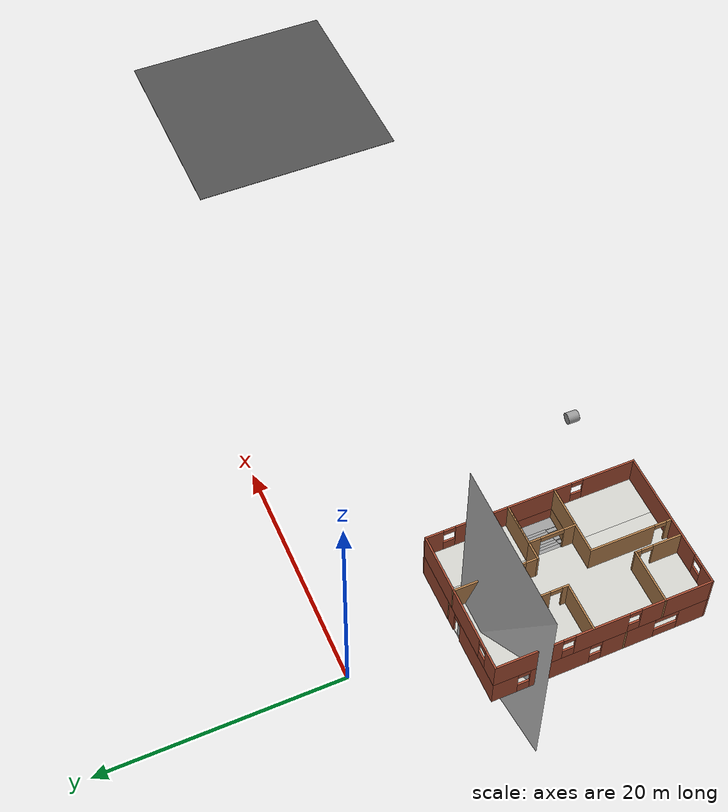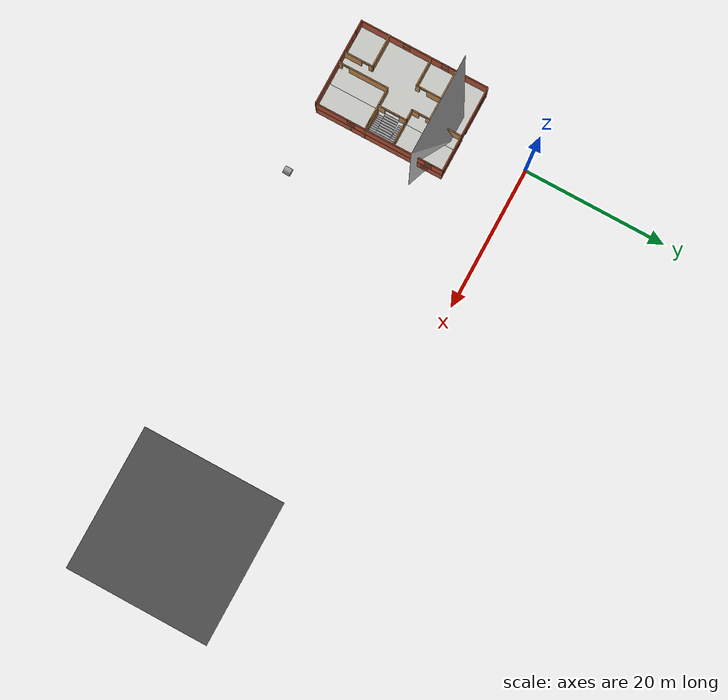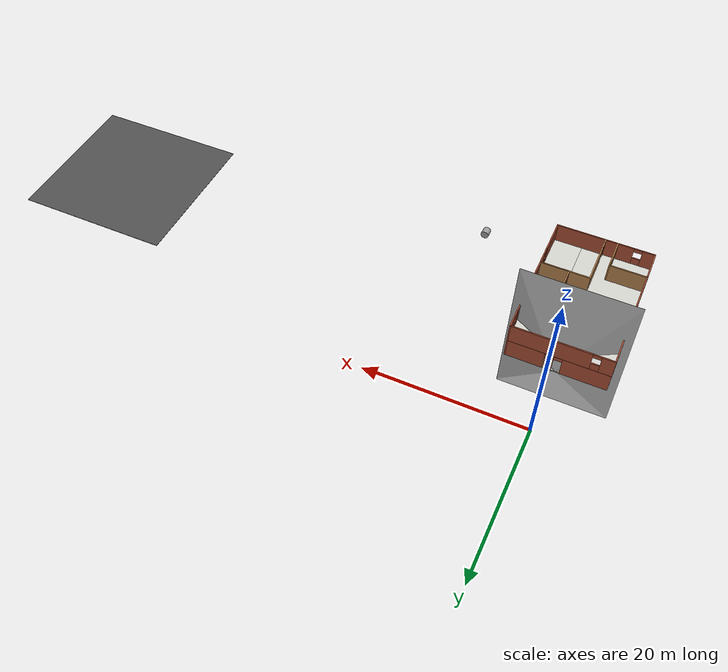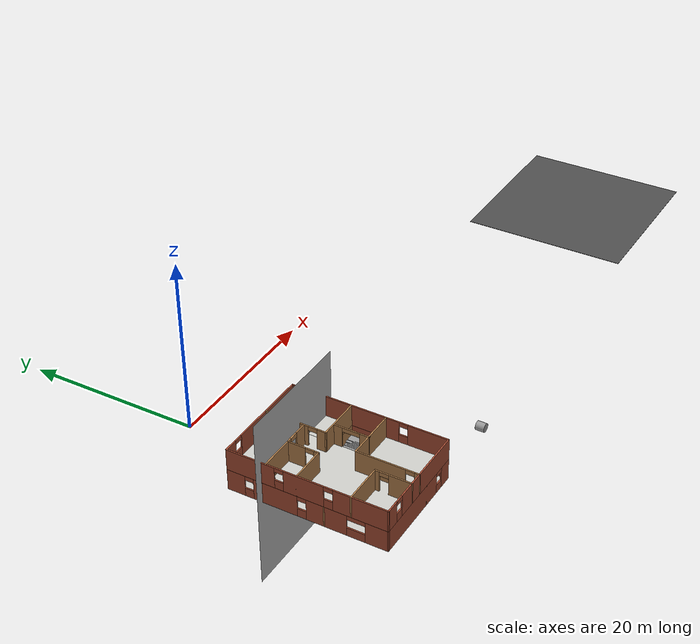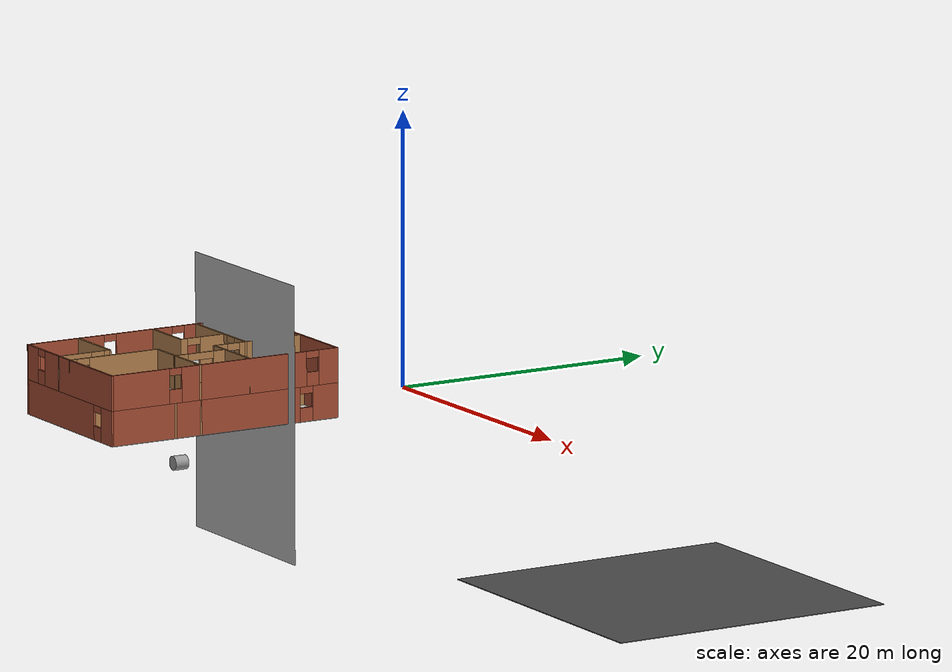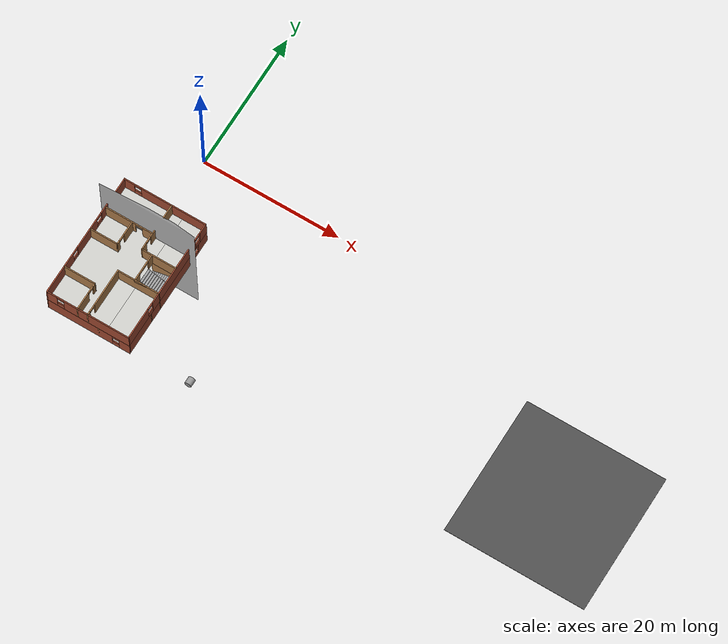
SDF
<sdf version="1.7">
 <world name="default">
  <scene>
   <grid>0</grid>
   <origin_visual>0</origin_visual>
   <ambient>0.592 0.624 0.635 1</ambient>
   <sky><clouds><speed>12</speed></clouds></sky>
   <background>0.35 0.35 0.35 1</background>
   <shadows>1</shadows>
  </scene>
  <physics name="default_physics" default="0" type="ode">
   <ode>
    <solver>
     <type>quick</type>
     <iters>10</iters>
     <sor>1.3</sor>
     <use_dynamic_moi_rescaling>0</use_dynamic_moi_rescaling>
    </solver>
    <constraints>
     <cfm>0</cfm>
     <erp>0.2</erp>
     <contact_max_correcting_vel>100</contact_max_correcting_vel>
     <contact_surface_layer>0.001</contact_surface_layer>
    </constraints>
   </ode>
   <max_step_size>0.001</max_step_size>
   <real_time_factor>1</real_time_factor>
   <real_time_update_rate>1000</real_time_update_rate>
  </physics>
  <plugin name="gazebo_ros_state" filename="libgazebo_ros_state.so">
   <ros><namespace>/gazebo</namespace></ros>
   <update_rate>20.0</update_rate>
  </plugin>
  <light name="sun" type="directional">
   <pose>0 0 1000 0 -0 0</pose>
   <diffuse>0.8 0.8 0.8 1</diffuse>
   <specular>0.5 0.5 0.5 1</specular>
   <attenuation>
    <range>1000</range>
    <constant>0.9</constant>
    <linear>0.01</linear>
    <quadratic>0.001</quadratic>
   </attenuation>
   <direction>-0.5 0.1 -0.4</direction>
   <spot><inner_angle>0</inner_angle><outer_angle>0</outer_angle><falloff>0</falloff></spot>
  </light>
  <model name="ground_plane">
   <static>1</static>
   <link name="link">
    <collision name="collision">
     <geometry><plane><normal>0 0 1</normal><size>100 100</size></plane></geometry>
     <friction><ode><mu>100</mu><mu2>50</mu2></ode></friction>
    </collision>
   </link>
  </model>
  <model name="asphalt_plane_74">
   <static>1</static>
   <pose>61.581 -16.664 0 0 -0 0</pose>
   <link name="link">
    <visual name="visual">
     <geometry><box><size>20 20 0.05</size></box></geometry>
     <material>
      <script>
       <uri>model://asphalt_plane/materials/scripts</uri>
       <uri>model://asphalt_plane/materials/textures</uri>
       <name>vrc/asphalt</name>
      </script>
     </material>
    </visual>
   </link>
  </model>
  <gravity>0 0 -9.8</gravity>
  <magnetic_field>6e-06 2.3e-05 -4.2e-05</magnetic_field>
  <atmosphere type="adiabatic"/>
  <spherical_coordinates>
   <surface_model>EARTH_WGS84</surface_model>
   <latitude_deg>0</latitude_deg>
   <longitude_deg>0</longitude_deg>
   <elevation>0</elevation>
   <heading_deg>0</heading_deg>
  </spherical_coordinates>
  <model name="unit_cylinder">
   <pose>14.5612 -26.5366 0.5 1.57081 -0.296633 -0.020703</pose>
   <link name="link">
    <inertial>
     <mass>1</mass>
     <inertia><ixx>0.145833</ixx><ixy>0</ixy><ixz>0</ixz><iyy>0.145833</iyy><iyz>0</iyz><izz>0.125</izz></inertia>
    </inertial>
    <collision name="collision">
     <geometry><cylinder><radius>0.5</radius><length>1</length></cylinder></geometry>
    </collision>
    <visual name="visual">
     <geometry><cylinder><radius>0.5</radius><length>1</length></cylinder></geometry>
     <material>
      <script><name>Gazebo/Grey</name><uri>file://media/materials/scripts/gazebo.material</uri></script>
     </material>
    </visual>
    <pose>-1.7763568394e-15 8.881784197e-16 -3.5527136788e-15 1.16636436837e-18 0 5.55111512313e-17</pose>
   </link>
  </model>
  <gravity>0 0 -9.8066</gravity>
  <magnetic_field>6e-06 2.3e-05 -4.2e-05</magnetic_field>
  <audio><device>default</device></audio>
  <model name="swarm_house">
   <frame name="demo_model::__model__" attached_to="demo_model::demo_wall_1_1">
    <pose relative_to="__model__">0 0 0 0 -0 0</pose>
   </frame>
   <static>1</static>
   <link name="demo_model::demo_wall_1_1">
    <pose relative_to="demo_model::__model__">-1.17691859741e-07 -9.00000000003 0 0 0 0</pose>
    <visual name="demo_wall_1_1_0_left_visual">
     <pose>-3.2875 0 1.25 0 -0 0</pose>
     <geometry><box><size>5.575 0.15 2.5</size></box></geometry>
     <material>
      <script><uri>file://media/materials/scripts/gazebo.material</uri><name>Gazebo/Bricks</name></script>
     </material>
     <meta><layer>0</layer></meta>
    </visual>
    <collision name="demo_wall_1_1_0_left_collision">
     <pose>-3.2875 0 1.25 0 -0 0</pose>
     <geometry><box><size>5.575 0.15 2.5</size></box></geometry>
     <surface>
      <bounce><threshold>1e+06</threshold></bounce>
      <contact>
       <ode><kp>1e+13</kp></ode>
       <bullet>
        <kp>1e+13</kp>
        <split_impulse>1</split_impulse>
        <split_impulse_penetration_threshold>-0.01</split_impulse_penetration_threshold>
       </bullet>
      </contact>
     </surface>
    </collision>
    <visual name="demo_wall_1_1_0_up_visual">
     <pose>0 0 2.25 0 -0 0</pose>
     <geometry><box><size>1 0.15 0.5</size></box></geometry>
     <material>
      <script><uri>file://media/materials/scripts/gazebo.material</uri><name>Gazebo/Bricks</name></script>
     </material>
     <meta><layer>0</layer></meta>
    </visual>
    <collision name="demo_wall_1_1_0_up_collision">
     <pose>0 0 2.25 0 -0 0</pose>
     <geometry><box><size>1 0.15 0.5</size></box></geometry>
     <surface>
      <bounce><threshold>1e+06</threshold></bounce>
      <contact>
       <ode><kp>1e+13</kp></ode>
       <bullet>
        <kp>1e+13</kp>
        <split_impulse>1</split_impulse>
        <split_impulse_penetration_threshold>-0.01</split_impulse_penetration_threshold>
       </bullet>
      </contact>
     </surface>
    </collision>
    <visual name="demo_wall_1_1_0_right_visual">
     <pose>3.2875 0 1.25 0 -0 0</pose>
     <geometry><box><size>5.575 0.15 2.5</size></box></geometry>
     <material>
      <script><uri>file://media/materials/scripts/gazebo.material</uri><name>Gazebo/Bricks</name></script>
     </material>
     <meta><layer>0</layer></meta>
    </visual>
    <collision name="demo_wall_1_1_0_right_collision">
     <pose>3.2875 0 1.25 0 -0 0</pose>
     <geometry><box><size>5.575 0.15 2.5</size></box></geometry>
     <surface>
      <bounce><threshold>1e+06</threshold></bounce>
      <contact>
       <ode><kp>1e+13</kp></ode>
       <bullet>
        <kp>1e+13</kp>
        <split_impulse>1</split_impulse>
        <split_impulse_penetration_threshold>-0.01</split_impulse_penetration_threshold>
       </bullet>
      </contact>
     </surface>
    </collision>
   </link>
   <link name="demo_model::demo_wall_1_2">
    <pose relative_to="demo_model::__model__">5.99997099998 1.59214618058e-05 0 0 0 1.57080530718</pose>
    <visual name="demo_wall_1_2_0_left_visual">
     <pose>-8.0375 0 1.25 0 -0 0</pose>
     <geometry><box><size>2.075 0.15 2.5</size></box></geometry>
     <material>
      <script><uri>file://media/materials/scripts/gazebo.material</uri><name>Gazebo/Bricks</name></script>
     </material>
     <meta><layer>0</layer></meta>
    </visual>
    <collision name="demo_wall_1_2_0_left_collision">
     <pose>-8.0375 0 1.25 0 -0 0</pose>
     <geometry><box><size>2.075 0.15 2.5</size></box></geometry>
     <surface>
      <bounce><threshold>1e+06</threshold></bounce>
      <contact>
       <ode><kp>1e+13</kp></ode>
       <bullet>
        <kp>1e+13</kp>
        <split_impulse>1</split_impulse>
        <split_impulse_penetration_threshold>-0.01</split_impulse_penetration_threshold>
       </bullet>
      </contact>
     </surface>
    </collision>
    <visual name="demo_wall_1_2_0_up_visual">
     <pose>-6.5 0 2.25 0 -0 0</pose>
     <geometry><box><size>1 0.15 0.5</size></box></geometry>
     <material>
      <script><uri>file://media/materials/scripts/gazebo.material</uri><name>Gazebo/Bricks</name></script>
     </material>
     <meta><layer>0</layer></meta>
    </visual>
    <collision name="demo_wall_1_2_0_up_collision">
     <pose>-6.5 0 2.25 0 -0 0</pose>
     <geometry><box><size>1 0.15 0.5</size></box></geometry>
     <surface>
      <bounce><threshold>1e+06</threshold></bounce>
      <contact>
       <ode><kp>1e+13</kp></ode>
       <bullet>
        <kp>1e+13</kp>
        <split_impulse>1</split_impulse>
        <split_impulse_penetration_threshold>-0.01</split_impulse_penetration_threshold>
       </bullet>
      </contact>
     </surface>
    </collision>
    <visual name="demo_wall_1_2_0_down_visual">
     <pose>-6.5 0 0.5 0 -0 0</pose>
     <geometry><box><size>1 0.15 1</size></box></geometry>
     <material>
      <script><uri>file://media/materials/scripts/gazebo.material</uri><name>Gazebo/Bricks</name></script>
     </material>
     <meta><layer>0</layer></meta>
    </visual>
    <collision name="demo_wall_1_2_0_down_collision">
     <pose>-6.5 0 0.5 0 -0 0</pose>
     <geometry><box><size>1 0.15 1</size></box></geometry>
     <surface>
      <bounce><threshold>1e+06</threshold></bounce>
      <contact>
       <ode><kp>1e+13</kp></ode>
       <bullet>
        <kp>1e+13</kp>
        <split_impulse>1</split_impulse>
        <split_impulse_penetration_threshold>-0.01</split_impulse_penetration_threshold>
       </bullet>
      </contact>
     </surface>
    </collision>
    <visual name="demo_wall_1_2_1_left_visual">
     <pose>-3.5 0 1.25 0 -0 0</pose>
     <geometry><box><size>5 0.15 2.5</size></box></geometry>
     <material>
      <script><uri>file://media/materials/scripts/gazebo.material</uri><name>Gazebo/Bricks</name></script>
     </material>
     <meta><layer>0</layer></meta>
    </visual>
    <collision name="demo_wall_1_2_1_left_collision">
     <pose>-3.5 0 1.25 0 -0 0</pose>
     <geometry><box><size>5 0.15 2.5</size></box></geometry>
     <surface>
      <bounce><threshold>1e+06</threshold></bounce>
      <contact>
       <ode><kp>1e+13</kp></ode>
       <bullet>
        <kp>1e+13</kp>
        <split_impulse>1</split_impulse>
        <split_impulse_penetration_threshold>-0.01</split_impulse_penetration_threshold>
       </bullet>
      </contact>
     </surface>
    </collision>
    <visual name="demo_wall_1_2_1_up_visual">
     <pose>-0.5 0 2.25 0 -0 0</pose>
     <geometry><box><size>1 0.15 0.5</size></box></geometry>
     <material>
      <script><uri>file://media/materials/scripts/gazebo.material</uri><name>Gazebo/Bricks</name></script>
     </material>
     <meta><layer>0</layer></meta>
    </visual>
    <collision name="demo_wall_1_2_1_up_collision">
     <pose>-0.5 0 2.25 0 -0 0</pose>
     <geometry><box><size>1 0.15 0.5</size></box></geometry>
     <surface>
      <bounce><threshold>1e+06</threshold></bounce>
      <contact>
       <ode><kp>1e+13</kp></ode>
       <bullet>
        <kp>1e+13</kp>
        <split_impulse>1</split_impulse>
        <split_impulse_penetration_threshold>-0.01</split_impulse_penetration_threshold>
       </bullet>
      </contact>
     </surface>
    </collision>
    <visual name="demo_wall_1_2_1_down_visual">
     <pose>-0.5 0 0.5 0 -0 0</pose>
     <geometry><box><size>1 0.15 1</size></box></geometry>
     <material>
      <script><uri>file://media/materials/scripts/gazebo.material</uri><name>Gazebo/Bricks</name></script>
     </material>
     <meta><layer>0</layer></meta>
    </visual>
    <collision name="demo_wall_1_2_1_down_collision">
     <pose>-0.5 0 0.5 0 -0 0</pose>
     <geometry><box><size>1 0.15 1</size></box></geometry>
     <surface>
      <bounce><threshold>1e+06</threshold></bounce>
      <contact>
       <ode><kp>1e+13</kp></ode>
       <bullet>
        <kp>1e+13</kp>
        <split_impulse>1</split_impulse>
        <split_impulse_penetration_threshold>-0.01</split_impulse_penetration_threshold>
       </bullet>
      </contact>
     </surface>
    </collision>
    <visual name="demo_wall_1_2_2_left_visual">
     <pose>2.25 0 1.25 0 -0 0</pose>
     <geometry><box><size>4.5 0.15 2.5</size></box></geometry>
     <material>
      <script><uri>file://media/materials/scripts/gazebo.material</uri><name>Gazebo/Bricks</name></script>
     </material>
     <meta><layer>0</layer></meta>
    </visual>
    <collision name="demo_wall_1_2_2_left_collision">
     <pose>2.25 0 1.25 0 -0 0</pose>
     <geometry><box><size>4.5 0.15 2.5</size></box></geometry>
     <surface>
      <bounce><threshold>1e+06</threshold></bounce>
      <contact>
       <ode><kp>1e+13</kp></ode>
       <bullet>
        <kp>1e+13</kp>
        <split_impulse>1</split_impulse>
        <split_impulse_penetration_threshold>-0.01</split_impulse_penetration_threshold>
       </bullet>
      </contact>
     </surface>
    </collision>
    <visual name="demo_wall_1_2_2_up_visual">
     <pose>5.5 0 2.25 0 -0 0</pose>
     <geometry><box><size>2 0.15 0.5</size></box></geometry>
     <material>
      <script><uri>file://media/materials/scripts/gazebo.material</uri><name>Gazebo/Bricks</name></script>
     </material>
     <meta><layer>0</layer></meta>
    </visual>
    <collision name="demo_wall_1_2_2_up_collision">
     <pose>5.5 0 2.25 0 -0 0</pose>
     <geometry><box><size>2 0.15 0.5</size></box></geometry>
     <surface>
      <bounce><threshold>1e+06</threshold></bounce>
      <contact>
       <ode><kp>1e+13</kp></ode>
       <bullet>
        <kp>1e+13</kp>
        <split_impulse>1</split_impulse>
        <split_impulse_penetration_threshold>-0.01</split_impulse_penetration_threshold>
       </bullet>
      </contact>
     </surface>
    </collision>
    <visual name="demo_wall_1_2_2_down_visual">
     <pose>5.5 0 0.5 0 -0 0</pose>
     <geometry><box><size>2 0.15 1</size></box></geometry>
     <material>
      <script><uri>file://media/materials/scripts/gazebo.material</uri><name>Gazebo/Bricks</name></script>
     </material>
     <meta><layer>0</layer></meta>
    </visual>
    <collision name="demo_wall_1_2_2_down_collision">
     <pose>5.5 0 0.5 0 -0 0</pose>
     <geometry><box><size>2 0.15 1</size></box></geometry>
     <surface>
      <bounce><threshold>1e+06</threshold></bounce>
      <contact>
       <ode><kp>1e+13</kp></ode>
       <bullet>
        <kp>1e+13</kp>
        <split_impulse>1</split_impulse>
        <split_impulse_penetration_threshold>-0.01</split_impulse_penetration_threshold>
       </bullet>
      </contact>
     </surface>
    </collision>
    <visual name="demo_wall_1_2_2_right_visual">
     <pose>7.7875 0 1.25 0 -0 0</pose>
     <geometry><box><size>2.575 0.15 2.5</size></box></geometry>
     <material>
      <script><uri>file://media/materials/scripts/gazebo.material</uri><name>Gazebo/Bricks</name></script>
     </material>
     <meta><layer>0</layer></meta>
    </visual>
    <collision name="demo_wall_1_2_2_right_collision">
     <pose>7.7875 0 1.25 0 -0 0</pose>
     <geometry><box><size>2.575 0.15 2.5</size></box></geometry>
     <surface>
      <bounce><threshold>1e+06</threshold></bounce>
      <contact>
       <ode><kp>1e+13</kp></ode>
       <bullet>
        <kp>1e+13</kp>
        <split_impulse>1</split_impulse>
        <split_impulse_penetration_threshold>-0.01</split_impulse_penetration_threshold>
       </bullet>
      </contact>
     </surface>
    </collision>
   </link>
   <link name="demo_model::demo_wall_1_3">
    <pose relative_to="demo_model::__model__">-5.38823081401e-05 8.99999999989 0 0 0 0</pose>
    <visual name="demo_wall_1_3_0_left_visual">
     <pose>-5.2875 0 1.25 0 -0 0</pose>
     <geometry><box><size>1.575 0.15 2.5</size></box></geometry>
     <material>
      <script><uri>file://media/materials/scripts/gazebo.material</uri><name>Gazebo/Bricks</name></script>
     </material>
     <meta><layer>0</layer></meta>
    </visual>
    <collision name="demo_wall_1_3_0_left_collision">
     <pose>-5.2875 0 1.25 0 -0 0</pose>
     <geometry><box><size>1.575 0.15 2.5</size></box></geometry>
     <surface>
      <bounce><threshold>1e+06</threshold></bounce>
      <contact>
       <ode><kp>1e+13</kp></ode>
       <bullet>
        <kp>1e+13</kp>
        <split_impulse>1</split_impulse>
        <split_impulse_penetration_threshold>-0.01</split_impulse_penetration_threshold>
       </bullet>
      </contact>
     </surface>
    </collision>
    <visual name="demo_wall_1_3_0_up_visual">
     <pose>-4 0 2.25 0 -0 0</pose>
     <geometry><box><size>1 0.15 0.5</size></box></geometry>
     <material>
      <script><uri>file://media/materials/scripts/gazebo.material</uri><name>Gazebo/Bricks</name></script>
     </material>
     <meta><layer>0</layer></meta>
    </visual>
    <collision name="demo_wall_1_3_0_up_collision">
     <pose>-4 0 2.25 0 -0 0</pose>
     <geometry><box><size>1 0.15 0.5</size></box></geometry>
     <surface>
      <bounce><threshold>1e+06</threshold></bounce>
      <contact>
       <ode><kp>1e+13</kp></ode>
       <bullet>
        <kp>1e+13</kp>
        <split_impulse>1</split_impulse>
        <split_impulse_penetration_threshold>-0.01</split_impulse_penetration_threshold>
       </bullet>
      </contact>
     </surface>
    </collision>
    <visual name="demo_wall_1_3_0_down_visual">
     <pose>-4 0 0.5 0 -0 0</pose>
     <geometry><box><size>1 0.15 1</size></box></geometry>
     <material>
      <script><uri>file://media/materials/scripts/gazebo.material</uri><name>Gazebo/Bricks</name></script>
     </material>
     <meta><layer>0</layer></meta>
    </visual>
    <collision name="demo_wall_1_3_0_down_collision">
     <pose>-4 0 0.5 0 -0 0</pose>
     <geometry><box><size>1 0.15 1</size></box></geometry>
     <surface>
      <bounce><threshold>1e+06</threshold></bounce>
      <contact>
       <ode><kp>1e+13</kp></ode>
       <bullet>
        <kp>1e+13</kp>
        <split_impulse>1</split_impulse>
        <split_impulse_penetration_threshold>-0.01</split_impulse_penetration_threshold>
       </bullet>
      </contact>
     </surface>
    </collision>
    <visual name="demo_wall_1_3_0_right_visual">
     <pose>1.2875 0 1.25 0 -0 0</pose>
     <geometry><box><size>9.575 0.15 2.5</size></box></geometry>
     <material>
      <script><uri>file://media/materials/scripts/gazebo.material</uri><name>Gazebo/Bricks</name></script>
     </material>
     <meta><layer>0</layer></meta>
    </visual>
    <collision name="demo_wall_1_3_0_right_collision">
     <pose>1.2875 0 1.25 0 -0 0</pose>
     <geometry><box><size>9.575 0.15 2.5</size></box></geometry>
     <surface>
      <bounce><threshold>1e+06</threshold></bounce>
      <contact>
       <ode><kp>1e+13</kp></ode>
       <bullet>
        <kp>1e+13</kp>
        <split_impulse>1</split_impulse>
        <split_impulse_penetration_threshold>-0.01</split_impulse_penetration_threshold>
       </bullet>
      </contact>
     </surface>
    </collision>
   </link>
   <link name="demo_model::demo_wall_1_4">
    <pose relative_to="demo_model::__model__">-6.00002899998 -1.5921615713e-05 0 0 0 -1.5708</pose>
    <visual name="demo_wall_1_4_0_left_visual">
     <pose>-1.5375 0 1.25 0 -0 0</pose>
     <geometry><box><size>15.075 0.15 2.5</size></box></geometry>
     <material>
      <script><uri>file://media/materials/scripts/gazebo.material</uri><name>Gazebo/Bricks</name></script>
     </material>
     <meta><layer>0</layer></meta>
    </visual>
    <collision name="demo_wall_1_4_0_left_collision">
     <pose>-1.5375 0 1.25 0 -0 0</pose>
     <geometry><box><size>15.075 0.15 2.5</size></box></geometry>
     <surface>
      <bounce><threshold>1e+06</threshold></bounce>
      <contact>
       <ode><kp>1e+13</kp></ode>
       <bullet>
        <kp>1e+13</kp>
        <split_impulse>1</split_impulse>
        <split_impulse_penetration_threshold>-0.01</split_impulse_penetration_threshold>
       </bullet>
      </contact>
     </surface>
    </collision>
    <visual name="demo_wall_1_4_0_up_visual">
     <pose>6.5 0 2.25 0 -0 0</pose>
     <geometry><box><size>1 0.15 0.5</size></box></geometry>
     <material>
      <script><uri>file://media/materials/scripts/gazebo.material</uri><name>Gazebo/Bricks</name></script>
     </material>
     <meta><layer>0</layer></meta>
    </visual>
    <collision name="demo_wall_1_4_0_up_collision">
     <pose>6.5 0 2.25 0 -0 0</pose>
     <geometry><box><size>1 0.15 0.5</size></box></geometry>
     <surface>
      <bounce><threshold>1e+06</threshold></bounce>
      <contact>
       <ode><kp>1e+13</kp></ode>
       <bullet>
        <kp>1e+13</kp>
        <split_impulse>1</split_impulse>
        <split_impulse_penetration_threshold>-0.01</split_impulse_penetration_threshold>
       </bullet>
      </contact>
     </surface>
    </collision>
    <visual name="demo_wall_1_4_0_down_visual">
     <pose>6.5 0 0.5 0 -0 0</pose>
     <geometry><box><size>1 0.15 1</size></box></geometry>
     <material>
      <script><uri>file://media/materials/scripts/gazebo.material</uri><name>Gazebo/Bricks</name></script>
     </material>
     <meta><layer>0</layer></meta>
    </visual>
    <collision name="demo_wall_1_4_0_down_collision">
     <pose>6.5 0 0.5 0 -0 0</pose>
     <geometry><box><size>1 0.15 1</size></box></geometry>
     <surface>
      <bounce><threshold>1e+06</threshold></bounce>
      <contact>
       <ode><kp>1e+13</kp></ode>
       <bullet>
        <kp>1e+13</kp>
        <split_impulse>1</split_impulse>
        <split_impulse_penetration_threshold>-0.01</split_impulse_penetration_threshold>
       </bullet>
      </contact>
     </surface>
    </collision>
    <visual name="demo_wall_1_4_0_right_visual">
     <pose>8.0375 0 1.25 0 -0 0</pose>
     <geometry><box><size>2.075 0.15 2.5</size></box></geometry>
     <material>
      <script><uri>file://media/materials/scripts/gazebo.material</uri><name>Gazebo/Bricks</name></script>
     </material>
     <meta><layer>0</layer></meta>
    </visual>
    <collision name="demo_wall_1_4_0_right_collision">
     <pose>8.0375 0 1.25 0 -0 0</pose>
     <geometry><box><size>2.075 0.15 2.5</size></box></geometry>
     <surface>
      <bounce><threshold>1e+06</threshold></bounce>
      <contact>
       <ode><kp>1e+13</kp></ode>
       <bullet>
        <kp>1e+13</kp>
        <split_impulse>1</split_impulse>
        <split_impulse_penetration_threshold>-0.01</split_impulse_penetration_threshold>
       </bullet>
      </contact>
     </surface>
    </collision>
   </link>
   <link name="demo_model::demo_wall_2_1">
    <pose relative_to="demo_model::__model__">-1.17691859741e-07 -9.00000000003 2.5 0 0 0</pose>
    <visual name="demo_wall_2_1_0_left_visual">
     <pose>-1.2875 0 1.25 0 -0 0</pose>
     <geometry><box><size>9.575 0.15 2.5</size></box></geometry>
     <material>
      <script><uri>file://media/materials/scripts/gazebo.material</uri><name>Gazebo/Bricks</name></script>
     </material>
     <meta><layer>1</layer></meta>
    </visual>
    <collision name="demo_wall_2_1_0_left_collision">
     <pose>-1.2875 0 1.25 0 -0 0</pose>
     <geometry><box><size>9.575 0.15 2.5</size></box></geometry>
     <surface>
      <bounce><threshold>1e+06</threshold></bounce>
      <contact>
       <ode><kp>1e+13</kp></ode>
       <bullet>
        <kp>1e+13</kp>
        <split_impulse>1</split_impulse>
        <split_impulse_penetration_threshold>-0.01</split_impulse_penetration_threshold>
       </bullet>
      </contact>
     </surface>
    </collision>
    <visual name="demo_wall_2_1_0_up_visual">
     <pose>4 0 2.25 0 -0 0</pose>
     <geometry><box><size>1 0.15 0.5</size></box></geometry>
     <material>
      <script><uri>file://media/materials/scripts/gazebo.material</uri><name>Gazebo/Bricks</name></script>
     </material>
     <meta><layer>1</layer></meta>
    </visual>
    <collision name="demo_wall_2_1_0_up_collision">
     <pose>4 0 2.25 0 -0 0</pose>
     <geometry><box><size>1 0.15 0.5</size></box></geometry>
     <surface>
      <bounce><threshold>1e+06</threshold></bounce>
      <contact>
       <ode><kp>1e+13</kp></ode>
       <bullet>
        <kp>1e+13</kp>
        <split_impulse>1</split_impulse>
        <split_impulse_penetration_threshold>-0.01</split_impulse_penetration_threshold>
       </bullet>
      </contact>
     </surface>
    </collision>
    <visual name="demo_wall_2_1_0_down_visual">
     <pose>4 0 0.5 0 -0 0</pose>
     <geometry><box><size>1 0.15 1</size></box></geometry>
     <material>
      <script><uri>file://media/materials/scripts/gazebo.material</uri><name>Gazebo/Bricks</name></script>
     </material>
     <meta><layer>1</layer></meta>
    </visual>
    <collision name="demo_wall_2_1_0_down_collision">
     <pose>4 0 0.5 0 -0 0</pose>
     <geometry><box><size>1 0.15 1</size></box></geometry>
     <surface>
      <bounce><threshold>1e+06</threshold></bounce>
      <contact>
       <ode><kp>1e+13</kp></ode>
       <bullet>
        <kp>1e+13</kp>
        <split_impulse>1</split_impulse>
        <split_impulse_penetration_threshold>-0.01</split_impulse_penetration_threshold>
       </bullet>
      </contact>
     </surface>
    </collision>
    <visual name="demo_wall_2_1_0_right_visual">
     <pose>5.2875 0 1.25 0 -0 0</pose>
     <geometry><box><size>1.575 0.15 2.5</size></box></geometry>
     <material>
      <script><uri>file://media/materials/scripts/gazebo.material</uri><name>Gazebo/Bricks</name></script>
     </material>
     <meta><layer>1</layer></meta>
    </visual>
    <collision name="demo_wall_2_1_0_right_collision">
     <pose>5.2875 0 1.25 0 -0 0</pose>
     <geometry><box><size>1.575 0.15 2.5</size></box></geometry>
     <surface>
      <bounce><threshold>1e+06</threshold></bounce>
      <contact>
       <ode><kp>1e+13</kp></ode>
       <bullet>
        <kp>1e+13</kp>
        <split_impulse>1</split_impulse>
        <split_impulse_penetration_threshold>-0.01</split_impulse_penetration_threshold>
       </bullet>
      </contact>
     </surface>
    </collision>
   </link>
   <link name="demo_model::demo_wall_2_2">
    <pose relative_to="demo_model::__model__">5.99997099998 1.59214618058e-05 2.5 0 0 1.57080530718</pose>
    <visual name="demo_wall_2_2_0_left_visual">
     <pose>-6.2875 0 1.25 0 -0 0</pose>
     <geometry><box><size>5.575 0.15 2.5</size></box></geometry>
     <material>
      <script><uri>file://media/materials/scripts/gazebo.material</uri><name>Gazebo/Bricks</name></script>
     </material>
     <meta><layer>1</layer></meta>
    </visual>
    <collision name="demo_wall_2_2_0_left_collision">
     <pose>-6.2875 0 1.25 0 -0 0</pose>
     <geometry><box><size>5.575 0.15 2.5</size></box></geometry>
     <surface>
      <bounce><threshold>1e+06</threshold></bounce>
      <contact>
       <ode><kp>1e+13</kp></ode>
       <bullet>
        <kp>1e+13</kp>
        <split_impulse>1</split_impulse>
        <split_impulse_penetration_threshold>-0.01</split_impulse_penetration_threshold>
       </bullet>
      </contact>
     </surface>
    </collision>
    <visual name="demo_wall_2_2_0_up_visual">
     <pose>-3 0 2.25 0 -0 0</pose>
     <geometry><box><size>1 0.15 0.5</size></box></geometry>
     <material>
      <script><uri>file://media/materials/scripts/gazebo.material</uri><name>Gazebo/Bricks</name></script>
     </material>
     <meta><layer>1</layer></meta>
    </visual>
    <collision name="demo_wall_2_2_0_up_collision">
     <pose>-3 0 2.25 0 -0 0</pose>
     <geometry><box><size>1 0.15 0.5</size></box></geometry>
     <surface>
      <bounce><threshold>1e+06</threshold></bounce>
      <contact>
       <ode><kp>1e+13</kp></ode>
       <bullet>
        <kp>1e+13</kp>
        <split_impulse>1</split_impulse>
        <split_impulse_penetration_threshold>-0.01</split_impulse_penetration_threshold>
       </bullet>
      </contact>
     </surface>
    </collision>
    <visual name="demo_wall_2_2_0_down_visual">
     <pose>-3 0 0.5 0 -0 0</pose>
     <geometry><box><size>1 0.15 1</size></box></geometry>
     <material>
      <script><uri>file://media/materials/scripts/gazebo.material</uri><name>Gazebo/Bricks</name></script>
     </material>
     <meta><layer>1</layer></meta>
    </visual>
    <collision name="demo_wall_2_2_0_down_collision">
     <pose>-3 0 0.5 0 -0 0</pose>
     <geometry><box><size>1 0.15 1</size></box></geometry>
     <surface>
      <bounce><threshold>1e+06</threshold></bounce>
      <contact>
       <ode><kp>1e+13</kp></ode>
       <bullet>
        <kp>1e+13</kp>
        <split_impulse>1</split_impulse>
        <split_impulse_penetration_threshold>-0.01</split_impulse_penetration_threshold>
       </bullet>
      </contact>
     </surface>
    </collision>
    <visual name="demo_wall_2_2_1_left_visual">
     <pose>-0.25 0 1.25 0 -0 0</pose>
     <geometry><box><size>4.5 0.15 2.5</size></box></geometry>
     <material>
      <script><uri>file://media/materials/scripts/gazebo.material</uri><name>Gazebo/Bricks</name></script>
     </material>
     <meta><layer>1</layer></meta>
    </visual>
    <collision name="demo_wall_2_2_1_left_collision">
     <pose>-0.25 0 1.25 0 -0 0</pose>
     <geometry><box><size>4.5 0.15 2.5</size></box></geometry>
     <surface>
      <bounce><threshold>1e+06</threshold></bounce>
      <contact>
       <ode><kp>1e+13</kp></ode>
       <bullet>
        <kp>1e+13</kp>
        <split_impulse>1</split_impulse>
        <split_impulse_penetration_threshold>-0.01</split_impulse_penetration_threshold>
       </bullet>
      </contact>
     </surface>
    </collision>
    <visual name="demo_wall_2_2_1_up_visual">
     <pose>2.5 0 2.25 0 -0 0</pose>
     <geometry><box><size>1 0.15 0.5</size></box></geometry>
     <material>
      <script><uri>file://media/materials/scripts/gazebo.material</uri><name>Gazebo/Bricks</name></script>
     </material>
     <meta><layer>1</layer></meta>
    </visual>
    <collision name="demo_wall_2_2_1_up_collision">
     <pose>2.5 0 2.25 0 -0 0</pose>
     <geometry><box><size>1 0.15 0.5</size></box></geometry>
     <surface>
      <bounce><threshold>1e+06</threshold></bounce>
      <contact>
       <ode><kp>1e+13</kp></ode>
       <bullet>
        <kp>1e+13</kp>
        <split_impulse>1</split_impulse>
        <split_impulse_penetration_threshold>-0.01</split_impulse_penetration_threshold>
       </bullet>
      </contact>
     </surface>
    </collision>
    <visual name="demo_wall_2_2_1_down_visual">
     <pose>2.5 0 0.5 0 -0 0</pose>
     <geometry><box><size>1 0.15 1</size></box></geometry>
     <material>
      <script><uri>file://media/materials/scripts/gazebo.material</uri><name>Gazebo/Bricks</name></script>
     </material>
     <meta><layer>1</layer></meta>
    </visual>
    <collision name="demo_wall_2_2_1_down_collision">
     <pose>2.5 0 0.5 0 -0 0</pose>
     <geometry><box><size>1 0.15 1</size></box></geometry>
     <surface>
      <bounce><threshold>1e+06</threshold></bounce>
      <contact>
       <ode><kp>1e+13</kp></ode>
       <bullet>
        <kp>1e+13</kp>
        <split_impulse>1</split_impulse>
        <split_impulse_penetration_threshold>-0.01</split_impulse_penetration_threshold>
       </bullet>
      </contact>
     </surface>
    </collision>
    <visual name="demo_wall_2_2_1_right_visual">
     <pose>6.0375 0 1.25 0 -0 0</pose>
     <geometry><box><size>6.075 0.15 2.5</size></box></geometry>
     <material>
      <script><uri>file://media/materials/scripts/gazebo.material</uri><name>Gazebo/Bricks</name></script>
     </material>
     <meta><layer>1</layer></meta>
    </visual>
    <collision name="demo_wall_2_2_1_right_collision">
     <pose>6.0375 0 1.25 0 -0 0</pose>
     <geometry><box><size>6.075 0.15 2.5</size></box></geometry>
     <surface>
      <bounce><threshold>1e+06</threshold></bounce>
      <contact>
       <ode><kp>1e+13</kp></ode>
       <bullet>
        <kp>1e+13</kp>
        <split_impulse>1</split_impulse>
        <split_impulse_penetration_threshold>-0.01</split_impulse_penetration_threshold>
       </bullet>
      </contact>
     </surface>
    </collision>
   </link>
   <link name="demo_model::demo_wall_2_3">
    <pose relative_to="demo_model::__model__">-5.38823081401e-05 8.99999999989 2.5 0 0 0</pose>
    <visual name="demo_wall_2_3_0_left_visual">
     <pose>-1.2875 0 1.25 0 -0 0</pose>
     <geometry><box><size>9.575 0.15 2.5</size></box></geometry>
     <material>
      <script><uri>file://media/materials/scripts/gazebo.material</uri><name>Gazebo/Bricks</name></script>
     </material>
     <meta><layer>1</layer></meta>
    </visual>
    <collision name="demo_wall_2_3_0_left_collision">
     <pose>-1.2875 0 1.25 0 -0 0</pose>
     <geometry><box><size>9.575 0.15 2.5</size></box></geometry>
     <surface>
      <bounce><threshold>1e+06</threshold></bounce>
      <contact>
       <ode><kp>1e+13</kp></ode>
       <bullet>
        <kp>1e+13</kp>
        <split_impulse>1</split_impulse>
        <split_impulse_penetration_threshold>-0.01</split_impulse_penetration_threshold>
       </bullet>
      </contact>
     </surface>
    </collision>
    <visual name="demo_wall_2_3_0_up_visual">
     <pose>4 0 2.25 0 -0 0</pose>
     <geometry><box><size>1 0.15 0.5</size></box></geometry>
     <material>
      <script><uri>file://media/materials/scripts/gazebo.material</uri><name>Gazebo/Bricks</name></script>
     </material>
     <meta><layer>1</layer></meta>
    </visual>
    <collision name="demo_wall_2_3_0_up_collision">
     <pose>4 0 2.25 0 -0 0</pose>
     <geometry><box><size>1 0.15 0.5</size></box></geometry>
     <surface>
      <bounce><threshold>1e+06</threshold></bounce>
      <contact>
       <ode><kp>1e+13</kp></ode>
       <bullet>
        <kp>1e+13</kp>
        <split_impulse>1</split_impulse>
        <split_impulse_penetration_threshold>-0.01</split_impulse_penetration_threshold>
       </bullet>
      </contact>
     </surface>
    </collision>
    <visual name="demo_wall_2_3_0_down_visual">
     <pose>4 0 0.5 0 -0 0</pose>
     <geometry><box><size>1 0.15 1</size></box></geometry>
     <material>
      <script><uri>file://media/materials/scripts/gazebo.material</uri><name>Gazebo/Bricks</name></script>
     </material>
     <meta><layer>1</layer></meta>
    </visual>
    <collision name="demo_wall_2_3_0_down_collision">
     <pose>4 0 0.5 0 -0 0</pose>
     <geometry><box><size>1 0.15 1</size></box></geometry>
     <surface>
      <bounce><threshold>1e+06</threshold></bounce>
      <contact>
       <ode><kp>1e+13</kp></ode>
       <bullet>
        <kp>1e+13</kp>
        <split_impulse>1</split_impulse>
        <split_impulse_penetration_threshold>-0.01</split_impulse_penetration_threshold>
       </bullet>
      </contact>
     </surface>
    </collision>
    <visual name="demo_wall_2_3_0_right_visual">
     <pose>5.2875 0 1.25 0 -0 0</pose>
     <geometry><box><size>1.575 0.15 2.5</size></box></geometry>
     <material>
      <script><uri>file://media/materials/scripts/gazebo.material</uri><name>Gazebo/Bricks</name></script>
     </material>
     <meta><layer>1</layer></meta>
    </visual>
    <collision name="demo_wall_2_3_0_right_collision">
     <pose>5.2875 0 1.25 0 -0 0</pose>
     <geometry><box><size>1.575 0.15 2.5</size></box></geometry>
     <surface>
      <bounce><threshold>1e+06</threshold></bounce>
      <contact>
       <ode><kp>1e+13</kp></ode>
       <bullet>
        <kp>1e+13</kp>
        <split_impulse>1</split_impulse>
        <split_impulse_penetration_threshold>-0.01</split_impulse_penetration_threshold>
       </bullet>
      </contact>
     </surface>
    </collision>
   </link>
   <link name="demo_model::demo_wall_2_4">
    <pose relative_to="demo_model::__model__">-6.00002899998 -1.5921615713e-05 2.5 0 0 -1.5708</pose>
    <visual name="demo_wall_2_4_0_left_visual">
     <pose>-6.7875 0 1.25 0 -0 0</pose>
     <geometry><box><size>4.575 0.15 2.5</size></box></geometry>
     <material>
      <script><uri>file://media/materials/scripts/gazebo.material</uri><name>Gazebo/Bricks</name></script>
     </material>
     <meta><layer>1</layer></meta>
    </visual>
    <collision name="demo_wall_2_4_0_left_collision">
     <pose>-6.7875 0 1.25 0 -0 0</pose>
     <geometry><box><size>4.575 0.15 2.5</size></box></geometry>
     <surface>
      <bounce><threshold>1e+06</threshold></bounce>
      <contact>
       <ode><kp>1e+13</kp></ode>
       <bullet>
        <kp>1e+13</kp>
        <split_impulse>1</split_impulse>
        <split_impulse_penetration_threshold>-0.01</split_impulse_penetration_threshold>
       </bullet>
      </contact>
     </surface>
    </collision>
    <visual name="demo_wall_2_4_0_up_visual">
     <pose>-4 0 2.25 0 -0 0</pose>
     <geometry><box><size>1 0.15 0.5</size></box></geometry>
     <material>
      <script><uri>file://media/materials/scripts/gazebo.material</uri><name>Gazebo/Bricks</name></script>
     </material>
     <meta><layer>1</layer></meta>
    </visual>
    <collision name="demo_wall_2_4_0_up_collision">
     <pose>-4 0 2.25 0 -0 0</pose>
     <geometry><box><size>1 0.15 0.5</size></box></geometry>
     <surface>
      <bounce><threshold>1e+06</threshold></bounce>
      <contact>
       <ode><kp>1e+13</kp></ode>
       <bullet>
        <kp>1e+13</kp>
        <split_impulse>1</split_impulse>
        <split_impulse_penetration_threshold>-0.01</split_impulse_penetration_threshold>
       </bullet>
      </contact>
     </surface>
    </collision>
    <visual name="demo_wall_2_4_0_down_visual">
     <pose>-4 0 0.5 0 -0 0</pose>
     <geometry><box><size>1 0.15 1</size></box></geometry>
     <material>
      <script><uri>file://media/materials/scripts/gazebo.material</uri><name>Gazebo/Bricks</name></script>
     </material>
     <meta><layer>1</layer></meta>
    </visual>
    <collision name="demo_wall_2_4_0_down_collision">
     <pose>-4 0 0.5 0 -0 0</pose>
     <geometry><box><size>1 0.15 1</size></box></geometry>
     <surface>
      <bounce><threshold>1e+06</threshold></bounce>
      <contact>
       <ode><kp>1e+13</kp></ode>
       <bullet>
        <kp>1e+13</kp>
        <split_impulse>1</split_impulse>
        <split_impulse_penetration_threshold>-0.01</split_impulse_penetration_threshold>
       </bullet>
      </contact>
     </surface>
    </collision>
    <visual name="demo_wall_2_4_1_left_visual">
     <pose>1.5 0 1.25 0 -0 0</pose>
     <geometry><box><size>10 0.15 2.5</size></box></geometry>
     <material>
      <script><uri>file://media/materials/scripts/gazebo.material</uri><name>Gazebo/Bricks</name></script>
     </material>
     <meta><layer>1</layer></meta>
    </visual>
    <collision name="demo_wall_2_4_1_left_collision">
     <pose>1.5 0 1.25 0 -0 0</pose>
     <geometry><box><size>10 0.15 2.5</size></box></geometry>
     <surface>
      <bounce><threshold>1e+06</threshold></bounce>
      <contact>
       <ode><kp>1e+13</kp></ode>
       <bullet>
        <kp>1e+13</kp>
        <split_impulse>1</split_impulse>
        <split_impulse_penetration_threshold>-0.01</split_impulse_penetration_threshold>
       </bullet>
      </contact>
     </surface>
    </collision>
    <visual name="demo_wall_2_4_1_up_visual">
     <pose>7 0 2.25 0 -0 0</pose>
     <geometry><box><size>1 0.15 0.5</size></box></geometry>
     <material>
      <script><uri>file://media/materials/scripts/gazebo.material</uri><name>Gazebo/Bricks</name></script>
     </material>
     <meta><layer>1</layer></meta>
    </visual>
    <collision name="demo_wall_2_4_1_up_collision">
     <pose>7 0 2.25 0 -0 0</pose>
     <geometry><box><size>1 0.15 0.5</size></box></geometry>
     <surface>
      <bounce><threshold>1e+06</threshold></bounce>
      <contact>
       <ode><kp>1e+13</kp></ode>
       <bullet>
        <kp>1e+13</kp>
        <split_impulse>1</split_impulse>
        <split_impulse_penetration_threshold>-0.01</split_impulse_penetration_threshold>
       </bullet>
      </contact>
     </surface>
    </collision>
    <visual name="demo_wall_2_4_1_down_visual">
     <pose>7 0 0.5 0 -0 0</pose>
     <geometry><box><size>1 0.15 1</size></box></geometry>
     <material>
      <script><uri>file://media/materials/scripts/gazebo.material</uri><name>Gazebo/Bricks</name></script>
     </material>
     <meta><layer>1</layer></meta>
    </visual>
    <collision name="demo_wall_2_4_1_down_collision">
     <pose>7 0 0.5 0 -0 0</pose>
     <geometry><box><size>1 0.15 1</size></box></geometry>
     <surface>
      <bounce><threshold>1e+06</threshold></bounce>
      <contact>
       <ode><kp>1e+13</kp></ode>
       <bullet>
        <kp>1e+13</kp>
        <split_impulse>1</split_impulse>
        <split_impulse_penetration_threshold>-0.01</split_impulse_penetration_threshold>
       </bullet>
      </contact>
     </surface>
    </collision>
    <visual name="demo_wall_2_4_1_right_visual">
     <pose>8.2875 0 1.25 0 -0 0</pose>
     <geometry><box><size>1.575 0.15 2.5</size></box></geometry>
     <material>
      <script><uri>file://media/materials/scripts/gazebo.material</uri><name>Gazebo/Bricks</name></script>
     </material>
     <meta><layer>1</layer></meta>
    </visual>
    <collision name="demo_wall_2_4_1_right_collision">
     <pose>8.2875 0 1.25 0 -0 0</pose>
     <geometry><box><size>1.575 0.15 2.5</size></box></geometry>
     <surface>
      <bounce><threshold>1e+06</threshold></bounce>
      <contact>
       <ode><kp>1e+13</kp></ode>
       <bullet>
        <kp>1e+13</kp>
        <split_impulse>1</split_impulse>
        <split_impulse_penetration_threshold>-0.01</split_impulse_penetration_threshold>
       </bullet>
      </contact>
     </surface>
    </collision>
   </link>
   <link name="demo_model::demo_wall_1_5">
    <pose relative_to="demo_model::__model__">-4.25003430716 1.99998872216 0 0 0 0</pose>
    <visual name="demo_wall_1_5_visual">
     <pose>0 0 1.25 0 -0 0</pose>
     <geometry><box><size>3.65 0.15 2.5</size></box></geometry>
     <material>
      <script><uri>file://media/materials/scripts/gazebo.material</uri><name>Gazebo/Wood</name></script>
     </material>
     <meta><layer>0</layer></meta>
    </visual>
    <collision name="demo_wall_1_5_collision">
     <pose>0 0 1.25 0 -0 0</pose>
     <geometry><box><size>3.65 0.15 2.5</size></box></geometry>
     <surface>
      <bounce><threshold>1e+06</threshold></bounce>
      <contact>
       <ode><kp>1e+13</kp></ode>
       <bullet>
        <kp>1e+13</kp>
        <split_impulse>1</split_impulse>
        <split_impulse_penetration_threshold>-0.01</split_impulse_penetration_threshold>
       </bullet>
      </contact>
     </surface>
    </collision>
   </link>
   <link name="demo_model::demo_wall_1_6">
    <pose relative_to="demo_model::__model__">-4.25002369281 -2.00001127783 0 0 0 0</pose>
    <visual name="demo_wall_1_6_visual">
     <pose>0 0 1.25 0 -0 0</pose>
     <geometry><box><size>3.65 0.15 2.5</size></box></geometry>
     <material>
      <script><uri>file://media/materials/scripts/gazebo.material</uri><name>Gazebo/Wood</name></script>
     </material>
     <meta><layer>0</layer></meta>
    </visual>
    <collision name="demo_wall_1_6_collision">
     <pose>0 0 1.25 0 -0 0</pose>
     <geometry><box><size>3.65 0.15 2.5</size></box></geometry>
     <surface>
      <bounce><threshold>1e+06</threshold></bounce>
      <contact>
       <ode><kp>1e+13</kp></ode>
       <bullet>
        <kp>1e+13</kp>
        <split_impulse>1</split_impulse>
        <split_impulse_penetration_threshold>-0.01</split_impulse_penetration_threshold>
       </bullet>
      </contact>
     </surface>
    </collision>
   </link>
   <link name="demo_model::demo_wall_1_7">
    <pose relative_to="demo_model::__model__">-3.75000838563 -4.000009951 0 0 0 0</pose>
    <visual name="demo_wall_1_7_0_left_visual">
     <pose>-1.2875 0 1.25 0 -0 0</pose>
     <geometry><box><size>2.075 0.15 2.5</size></box></geometry>
     <material>
      <script><uri>file://media/materials/scripts/gazebo.material</uri><name>Gazebo/Wood</name></script>
     </material>
     <meta><layer>0</layer></meta>
    </visual>
    <collision name="demo_wall_1_7_0_left_collision">
     <pose>-1.2875 0 1.25 0 -0 0</pose>
     <geometry><box><size>2.075 0.15 2.5</size></box></geometry>
     <surface>
      <bounce><threshold>1e+06</threshold></bounce>
      <contact>
       <ode><kp>1e+13</kp></ode>
       <bullet>
        <kp>1e+13</kp>
        <split_impulse>1</split_impulse>
        <split_impulse_penetration_threshold>-0.01</split_impulse_penetration_threshold>
       </bullet>
      </contact>
     </surface>
    </collision>
    <visual name="demo_wall_1_7_0_up_visual">
     <pose>0.25 0 2.25 0 -0 0</pose>
     <geometry><box><size>1 0.15 0.5</size></box></geometry>
     <material>
      <script><uri>file://media/materials/scripts/gazebo.material</uri><name>Gazebo/Wood</name></script>
     </material>
     <meta><layer>0</layer></meta>
    </visual>
    <collision name="demo_wall_1_7_0_up_collision">
     <pose>0.25 0 2.25 0 -0 0</pose>
     <geometry><box><size>1 0.15 0.5</size></box></geometry>
     <surface>
      <bounce><threshold>1e+06</threshold></bounce>
      <contact>
       <ode><kp>1e+13</kp></ode>
       <bullet>
        <kp>1e+13</kp>
        <split_impulse>1</split_impulse>
        <split_impulse_penetration_threshold>-0.01</split_impulse_penetration_threshold>
       </bullet>
      </contact>
     </surface>
    </collision>
    <visual name="demo_wall_1_7_0_right_visual">
     <pose>1.5375 0 1.25 0 -0 0</pose>
     <geometry><box><size>1.575 0.15 2.5</size></box></geometry>
     <material>
      <script><uri>file://media/materials/scripts/gazebo.material</uri><name>Gazebo/Wood</name></script>
     </material>
     <meta><layer>0</layer></meta>
    </visual>
    <collision name="demo_wall_1_7_0_right_collision">
     <pose>1.5375 0 1.25 0 -0 0</pose>
     <geometry><box><size>1.575 0.15 2.5</size></box></geometry>
     <surface>
      <bounce><threshold>1e+06</threshold></bounce>
      <contact>
       <ode><kp>1e+13</kp></ode>
       <bullet>
        <kp>1e+13</kp>
        <split_impulse>1</split_impulse>
        <split_impulse_penetration_threshold>-0.01</split_impulse_penetration_threshold>
       </bullet>
      </contact>
     </surface>
    </collision>
   </link>
   <link name="demo_model::demo_wall_1_8">
    <pose relative_to="demo_model::__model__">-1.50000175166 -6.50000398041 0 0 0 1.57080530718</pose>
    <visual name="demo_wall_1_8_visual">
     <pose>0 0 1.25 0 -0 0</pose>
     <geometry><box><size>5.15 0.15 2.5</size></box></geometry>
     <material>
      <script><uri>file://media/materials/scripts/gazebo.material</uri><name>Gazebo/Wood</name></script>
     </material>
     <meta><layer>0</layer></meta>
    </visual>
    <collision name="demo_wall_1_8_collision">
     <pose>0 0 1.25 0 -0 0</pose>
     <geometry><box><size>5.15 0.15 2.5</size></box></geometry>
     <surface>
      <bounce><threshold>1e+06</threshold></bounce>
      <contact>
       <ode><kp>1e+13</kp></ode>
       <bullet>
        <kp>1e+13</kp>
        <split_impulse>1</split_impulse>
        <split_impulse_penetration_threshold>-0.01</split_impulse_penetration_threshold>
       </bullet>
      </contact>
     </surface>
    </collision>
   </link>
   <link name="demo_model::demo_wall_1_9">
    <pose relative_to="demo_model::__model__">3.74998896076 -2.99999004908 0 0 0 0</pose>
    <visual name="demo_wall_1_9_0_left_visual">
     <pose>-1.0375 0 1.25 0 -0 0</pose>
     <geometry><box><size>2.575 0.15 2.5</size></box></geometry>
     <material>
      <script><uri>file://media/materials/scripts/gazebo.material</uri><name>Gazebo/Wood</name></script>
     </material>
     <meta><layer>0</layer></meta>
    </visual>
    <collision name="demo_wall_1_9_0_left_collision">
     <pose>-1.0375 0 1.25 0 -0 0</pose>
     <geometry><box><size>2.575 0.15 2.5</size></box></geometry>
     <surface>
      <bounce><threshold>1e+06</threshold></bounce>
      <contact>
       <ode><kp>1e+13</kp></ode>
       <bullet>
        <kp>1e+13</kp>
        <split_impulse>1</split_impulse>
        <split_impulse_penetration_threshold>-0.01</split_impulse_penetration_threshold>
       </bullet>
      </contact>
     </surface>
    </collision>
    <visual name="demo_wall_1_9_0_up_visual">
     <pose>0.75 0 2.25 0 -0 0</pose>
     <geometry><box><size>1 0.15 0.5</size></box></geometry>
     <material>
      <script><uri>file://media/materials/scripts/gazebo.material</uri><name>Gazebo/Wood</name></script>
     </material>
     <meta><layer>0</layer></meta>
    </visual>
    <collision name="demo_wall_1_9_0_up_collision">
     <pose>0.75 0 2.25 0 -0 0</pose>
     <geometry><box><size>1 0.15 0.5</size></box></geometry>
     <surface>
      <bounce><threshold>1e+06</threshold></bounce>
      <contact>
       <ode><kp>1e+13</kp></ode>
       <bullet>
        <kp>1e+13</kp>
        <split_impulse>1</split_impulse>
        <split_impulse_penetration_threshold>-0.01</split_impulse_penetration_threshold>
       </bullet>
      </contact>
     </surface>
    </collision>
    <visual name="demo_wall_1_9_0_right_visual">
     <pose>1.7875 0 1.25 0 -0 0</pose>
     <geometry><box><size>1.075 0.15 2.5</size></box></geometry>
     <material>
      <script><uri>file://media/materials/scripts/gazebo.material</uri><name>Gazebo/Wood</name></script>
     </material>
     <meta><layer>0</layer></meta>
    </visual>
    <collision name="demo_wall_1_9_0_right_collision">
     <pose>1.7875 0 1.25 0 -0 0</pose>
     <geometry><box><size>1.075 0.15 2.5</size></box></geometry>
     <surface>
      <bounce><threshold>1e+06</threshold></bounce>
      <contact>
       <ode><kp>1e+13</kp></ode>
       <bullet>
        <kp>1e+13</kp>
        <split_impulse>1</split_impulse>
        <split_impulse_penetration_threshold>-0.01</split_impulse_penetration_threshold>
       </bullet>
      </contact>
     </surface>
    </collision>
   </link>
   <link name="demo_model::demo_wall_1_10">
    <pose relative_to="demo_model::__model__">1.49999692153 -5.99999601964 0 0 0 1.57080530718</pose>
    <visual name="demo_wall_1_10_visual">
     <pose>0 0 1.25 0 -0 0</pose>
     <geometry><box><size>6.15 0.15 2.5</size></box></geometry>
     <material>
      <script><uri>file://media/materials/scripts/gazebo.material</uri><name>Gazebo/Wood</name></script>
     </material>
     <meta><layer>0</layer></meta>
    </visual>
    <collision name="demo_wall_1_10_collision">
     <pose>0 0 1.25 0 -0 0</pose>
     <geometry><box><size>6.15 0.15 2.5</size></box></geometry>
     <surface>
      <bounce><threshold>1e+06</threshold></bounce>
      <contact>
       <ode><kp>1e+13</kp></ode>
       <bullet>
        <kp>1e+13</kp>
        <split_impulse>1</split_impulse>
        <split_impulse_penetration_threshold>-0.01</split_impulse_penetration_threshold>
       </bullet>
      </contact>
     </surface>
    </collision>
   </link>
   <link name="demo_model::demo_wall_1_11">
    <pose relative_to="demo_model::__model__">2.99996569281 2.00000796069 0 0 0 0</pose>
    <visual name="demo_wall_1_11_visual">
     <pose>0 0 1.25 0 -0 0</pose>
     <geometry><box><size>6.15 0.15 2.5</size></box></geometry>
     <material>
      <script><uri>file://media/materials/scripts/gazebo.material</uri><name>Gazebo/Wood</name></script>
     </material>
     <meta><layer>0</layer></meta>
    </visual>
    <collision name="demo_wall_1_11_collision">
     <pose>0 0 1.25 0 -0 0</pose>
     <geometry><box><size>6.15 0.15 2.5</size></box></geometry>
     <surface>
      <bounce><threshold>1e+06</threshold></bounce>
      <contact>
       <ode><kp>1e+13</kp></ode>
       <bullet>
        <kp>1e+13</kp>
        <split_impulse>1</split_impulse>
        <split_impulse_penetration_threshold>-0.01</split_impulse_penetration_threshold>
       </bullet>
      </contact>
     </surface>
    </collision>
   </link>
   <link name="demo_model::demo_wall_1_12">
    <pose relative_to="demo_model::__model__">-3.75003961435 3.99999004895 0 0 0 0</pose>
    <visual name="demo_wall_1_12_visual">
     <pose>0 0 1.25 0 -0 0</pose>
     <geometry><box><size>4.65 0.15 2.5</size></box></geometry>
     <material>
      <script><uri>file://media/materials/scripts/gazebo.material</uri><name>Gazebo/Wood</name></script>
     </material>
     <meta><layer>0</layer></meta>
    </visual>
    <collision name="demo_wall_1_12_collision">
     <pose>0 0 1.25 0 -0 0</pose>
     <geometry><box><size>4.65 0.15 2.5</size></box></geometry>
     <surface>
      <bounce><threshold>1e+06</threshold></bounce>
      <contact>
       <ode><kp>1e+13</kp></ode>
       <bullet>
        <kp>1e+13</kp>
        <split_impulse>1</split_impulse>
        <split_impulse_penetration_threshold>-0.01</split_impulse_penetration_threshold>
       </bullet>
      </contact>
     </surface>
    </collision>
   </link>
   <link name="demo_model::demo_wall_1_13">
    <pose relative_to="demo_model::__model__">-1.50004624833 6.49999601952 0 0 0 1.57080530718</pose>
    <visual name="demo_wall_1_13_0_left_visual">
     <pose>-1.5375 0 1.25 0 -0 0</pose>
     <geometry><box><size>2.075 0.15 2.5</size></box></geometry>
     <material>
      <script><uri>file://media/materials/scripts/gazebo.material</uri><name>Gazebo/Wood</name></script>
     </material>
     <meta><layer>0</layer></meta>
    </visual>
    <collision name="demo_wall_1_13_0_left_collision">
     <pose>-1.5375 0 1.25 0 -0 0</pose>
     <geometry><box><size>2.075 0.15 2.5</size></box></geometry>
     <surface>
      <bounce><threshold>1e+06</threshold></bounce>
      <contact>
       <ode><kp>1e+13</kp></ode>
       <bullet>
        <kp>1e+13</kp>
        <split_impulse>1</split_impulse>
        <split_impulse_penetration_threshold>-0.01</split_impulse_penetration_threshold>
       </bullet>
      </contact>
     </surface>
    </collision>
    <visual name="demo_wall_1_13_0_up_visual">
     <pose>0 0 2.25 0 -0 0</pose>
     <geometry><box><size>1 0.15 0.5</size></box></geometry>
     <material>
      <script><uri>file://media/materials/scripts/gazebo.material</uri><name>Gazebo/Wood</name></script>
     </material>
     <meta><layer>0</layer></meta>
    </visual>
    <collision name="demo_wall_1_13_0_up_collision">
     <pose>0 0 2.25 0 -0 0</pose>
     <geometry><box><size>1 0.15 0.5</size></box></geometry>
     <surface>
      <bounce><threshold>1e+06</threshold></bounce>
      <contact>
       <ode><kp>1e+13</kp></ode>
       <bullet>
        <kp>1e+13</kp>
        <split_impulse>1</split_impulse>
        <split_impulse_penetration_threshold>-0.01</split_impulse_penetration_threshold>
       </bullet>
      </contact>
     </surface>
    </collision>
    <visual name="demo_wall_1_13_0_right_visual">
     <pose>1.5375 0 1.25 0 -0 0</pose>
     <geometry><box><size>2.075 0.15 2.5</size></box></geometry>
     <material>
      <script><uri>file://media/materials/scripts/gazebo.material</uri><name>Gazebo/Wood</name></script>
     </material>
     <meta><layer>0</layer></meta>
    </visual>
    <collision name="demo_wall_1_13_0_right_collision">
     <pose>1.5375 0 1.25 0 -0 0</pose>
     <geometry><box><size>2.075 0.15 2.5</size></box></geometry>
     <surface>
      <bounce><threshold>1e+06</threshold></bounce>
      <contact>
       <ode><kp>1e+13</kp></ode>
       <bullet>
        <kp>1e+13</kp>
        <split_impulse>1</split_impulse>
        <split_impulse_penetration_threshold>-0.01</split_impulse_penetration_threshold>
       </bullet>
      </contact>
     </surface>
    </collision>
   </link>
   <link name="demo_model::demo_wall_2_5">
    <pose relative_to="demo_model::__model__">-4.25003430716 1.99998872216 2.5 0 0 0</pose>
    <visual name="demo_wall_2_5_visual">
     <pose>0 0 1.25 0 -0 0</pose>
     <geometry><box><size>3.65 0.15 2.5</size></box></geometry>
     <material>
      <script><uri>file://media/materials/scripts/gazebo.material</uri><name>Gazebo/Wood</name></script>
     </material>
     <meta><layer>1</layer></meta>
    </visual>
    <collision name="demo_wall_2_5_collision">
     <pose>0 0 1.25 0 -0 0</pose>
     <geometry><box><size>3.65 0.15 2.5</size></box></geometry>
     <surface>
      <bounce><threshold>1e+06</threshold></bounce>
      <contact>
       <ode><kp>1e+13</kp></ode>
       <bullet>
        <kp>1e+13</kp>
        <split_impulse>1</split_impulse>
        <split_impulse_penetration_threshold>-0.01</split_impulse_penetration_threshold>
       </bullet>
      </contact>
     </surface>
    </collision>
   </link>
   <link name="demo_model::demo_wall_2_6">
    <pose relative_to="demo_model::__model__">-4.25002369281 -2.00001127783 2.5 0 0 0</pose>
    <visual name="demo_wall_2_6_visual">
     <pose>0 0 1.25 0 -0 0</pose>
     <geometry><box><size>3.65 0.15 2.5</size></box></geometry>
     <material>
      <script><uri>file://media/materials/scripts/gazebo.material</uri><name>Gazebo/Wood</name></script>
     </material>
     <meta><layer>1</layer></meta>
    </visual>
    <collision name="demo_wall_2_6_collision">
     <pose>0 0 1.25 0 -0 0</pose>
     <geometry><box><size>3.65 0.15 2.5</size></box></geometry>
     <surface>
      <bounce><threshold>1e+06</threshold></bounce>
      <contact>
       <ode><kp>1e+13</kp></ode>
       <bullet>
        <kp>1e+13</kp>
        <split_impulse>1</split_impulse>
        <split_impulse_penetration_threshold>-0.01</split_impulse_penetration_threshold>
       </bullet>
      </contact>
     </surface>
    </collision>
   </link>
   <link name="demo_model::demo_wall_2_7">
    <pose relative_to="demo_model::__model__">-2.50002899999 -6.63405143797e-06 2.5 0 0 1.57080530718</pose>
    <visual name="demo_wall_2_7_0_left_visual">
     <pose>-1.5375 0 1.25 0 -0 0</pose>
     <geometry><box><size>1.075 0.15 2.5</size></box></geometry>
     <material>
      <script><uri>file://media/materials/scripts/gazebo.material</uri><name>Gazebo/Wood</name></script>
     </material>
     <meta><layer>1</layer></meta>
    </visual>
    <collision name="demo_wall_2_7_0_left_collision">
     <pose>-1.5375 0 1.25 0 -0 0</pose>
     <geometry><box><size>1.075 0.15 2.5</size></box></geometry>
     <surface>
      <bounce><threshold>1e+06</threshold></bounce>
      <contact>
       <ode><kp>1e+13</kp></ode>
       <bullet>
        <kp>1e+13</kp>
        <split_impulse>1</split_impulse>
        <split_impulse_penetration_threshold>-0.01</split_impulse_penetration_threshold>
       </bullet>
      </contact>
     </surface>
    </collision>
    <visual name="demo_wall_2_7_0_up_visual">
     <pose>0 0 2.25 0 -0 0</pose>
     <geometry><box><size>2 0.15 0.5</size></box></geometry>
     <material>
      <script><uri>file://media/materials/scripts/gazebo.material</uri><name>Gazebo/Wood</name></script>
     </material>
     <meta><layer>1</layer></meta>
    </visual>
    <collision name="demo_wall_2_7_0_up_collision">
     <pose>0 0 2.25 0 -0 0</pose>
     <geometry><box><size>2 0.15 0.5</size></box></geometry>
     <surface>
      <bounce><threshold>1e+06</threshold></bounce>
      <contact>
       <ode><kp>1e+13</kp></ode>
       <bullet>
        <kp>1e+13</kp>
        <split_impulse>1</split_impulse>
        <split_impulse_penetration_threshold>-0.01</split_impulse_penetration_threshold>
       </bullet>
      </contact>
     </surface>
    </collision>
    <visual name="demo_wall_2_7_0_right_visual">
     <pose>1.5375 0 1.25 0 -0 0</pose>
     <geometry><box><size>1.075 0.15 2.5</size></box></geometry>
     <material>
      <script><uri>file://media/materials/scripts/gazebo.material</uri><name>Gazebo/Wood</name></script>
     </material>
     <meta><layer>1</layer></meta>
    </visual>
    <collision name="demo_wall_2_7_0_right_collision">
     <pose>1.5375 0 1.25 0 -0 0</pose>
     <geometry><box><size>1.075 0.15 2.5</size></box></geometry>
     <surface>
      <bounce><threshold>1e+06</threshold></bounce>
      <contact>
       <ode><kp>1e+13</kp></ode>
       <bullet>
        <kp>1e+13</kp>
        <split_impulse>1</split_impulse>
        <split_impulse_penetration_threshold>-0.01</split_impulse_penetration_threshold>
       </bullet>
      </contact>
     </surface>
    </collision>
   </link>
   <link name="demo_model::demo_wall_2_8">
    <pose relative_to="demo_model::__model__">-3.50002369281 -2.00000928763 2.5 0 0 0</pose>
    <visual name="demo_wall_2_8_visual">
     <pose>0 0 1.25 0 -0 0</pose>
     <geometry><box><size>5.15 0.15 2.5</size></box></geometry>
     <material>
      <script><uri>file://media/materials/scripts/gazebo.material</uri><name>Gazebo/Wood</name></script>
     </material>
     <meta><layer>1</layer></meta>
    </visual>
    <collision name="demo_wall_2_8_collision">
     <pose>0 0 1.25 0 -0 0</pose>
     <geometry><box><size>5.15 0.15 2.5</size></box></geometry>
     <surface>
      <bounce><threshold>1e+06</threshold></bounce>
      <contact>
       <ode><kp>1e+13</kp></ode>
       <bullet>
        <kp>1e+13</kp>
        <split_impulse>1</split_impulse>
        <split_impulse_penetration_threshold>-0.01</split_impulse_penetration_threshold>
       </bullet>
      </contact>
     </surface>
    </collision>
   </link>
   <link name="demo_model::demo_wall_2_9">
    <pose relative_to="demo_model::__model__">-1.00000440525 -5.50000265362 2.5 0 0 1.57080530718</pose>
    <visual name="demo_wall_2_9_0_left_visual">
     <pose>-1.0375 0 1.25 0 -0 0</pose>
     <geometry><box><size>5.075 0.15 2.5</size></box></geometry>
     <material>
      <script><uri>file://media/materials/scripts/gazebo.material</uri><name>Gazebo/Wood</name></script>
     </material>
     <meta><layer>1</layer></meta>
    </visual>
    <collision name="demo_wall_2_9_0_left_collision">
     <pose>-1.0375 0 1.25 0 -0 0</pose>
     <geometry><box><size>5.075 0.15 2.5</size></box></geometry>
     <surface>
      <bounce><threshold>1e+06</threshold></bounce>
      <contact>
       <ode><kp>1e+13</kp></ode>
       <bullet>
        <kp>1e+13</kp>
        <split_impulse>1</split_impulse>
        <split_impulse_penetration_threshold>-0.01</split_impulse_penetration_threshold>
       </bullet>
      </contact>
     </surface>
    </collision>
    <visual name="demo_wall_2_9_0_up_visual">
     <pose>2 0 2.25 0 -0 0</pose>
     <geometry><box><size>1 0.15 0.5</size></box></geometry>
     <material>
      <script><uri>file://media/materials/scripts/gazebo.material</uri><name>Gazebo/Wood</name></script>
     </material>
     <meta><layer>1</layer></meta>
    </visual>
    <collision name="demo_wall_2_9_0_up_collision">
     <pose>2 0 2.25 0 -0 0</pose>
     <geometry><box><size>1 0.15 0.5</size></box></geometry>
     <surface>
      <bounce><threshold>1e+06</threshold></bounce>
      <contact>
       <ode><kp>1e+13</kp></ode>
       <bullet>
        <kp>1e+13</kp>
        <split_impulse>1</split_impulse>
        <split_impulse_penetration_threshold>-0.01</split_impulse_penetration_threshold>
       </bullet>
      </contact>
     </surface>
    </collision>
    <visual name="demo_wall_2_9_0_right_visual">
     <pose>3.0375 0 1.25 0 -0 0</pose>
     <geometry><box><size>1.075 0.15 2.5</size></box></geometry>
     <material>
      <script><uri>file://media/materials/scripts/gazebo.material</uri><name>Gazebo/Wood</name></script>
     </material>
     <meta><layer>1</layer></meta>
    </visual>
    <collision name="demo_wall_2_9_0_right_collision">
     <pose>3.0375 0 1.25 0 -0 0</pose>
     <geometry><box><size>1.075 0.15 2.5</size></box></geometry>
     <surface>
      <bounce><threshold>1e+06</threshold></bounce>
      <contact>
       <ode><kp>1e+13</kp></ode>
       <bullet>
        <kp>1e+13</kp>
        <split_impulse>1</split_impulse>
        <split_impulse_penetration_threshold>-0.01</split_impulse_penetration_threshold>
       </bullet>
      </contact>
     </surface>
    </collision>
   </link>
   <link name="demo_model::demo_wall_2_10">
    <pose relative_to="demo_model::__model__">2.49999294115 -4.49999336606 2.5 0 0 0</pose>
    <visual name="demo_wall_2_10_0_left_visual">
     <pose>-2.7875 0 1.25 0 -0 0</pose>
     <geometry><box><size>1.575 0.15 2.5</size></box></geometry>
     <material>
      <script><uri>file://media/materials/scripts/gazebo.material</uri><name>Gazebo/Wood</name></script>
     </material>
     <meta><layer>1</layer></meta>
    </visual>
    <collision name="demo_wall_2_10_0_left_collision">
     <pose>-2.7875 0 1.25 0 -0 0</pose>
     <geometry><box><size>1.575 0.15 2.5</size></box></geometry>
     <surface>
      <bounce><threshold>1e+06</threshold></bounce>
      <contact>
       <ode><kp>1e+13</kp></ode>
       <bullet>
        <kp>1e+13</kp>
        <split_impulse>1</split_impulse>
        <split_impulse_penetration_threshold>-0.01</split_impulse_penetration_threshold>
       </bullet>
      </contact>
     </surface>
    </collision>
    <visual name="demo_wall_2_10_0_up_visual">
     <pose>-1.5 0 2.25 0 -0 0</pose>
     <geometry><box><size>1 0.15 0.5</size></box></geometry>
     <material>
      <script><uri>file://media/materials/scripts/gazebo.material</uri><name>Gazebo/Wood</name></script>
     </material>
     <meta><layer>1</layer></meta>
    </visual>
    <collision name="demo_wall_2_10_0_up_collision">
     <pose>-1.5 0 2.25 0 -0 0</pose>
     <geometry><box><size>1 0.15 0.5</size></box></geometry>
     <surface>
      <bounce><threshold>1e+06</threshold></bounce>
      <contact>
       <ode><kp>1e+13</kp></ode>
       <bullet>
        <kp>1e+13</kp>
        <split_impulse>1</split_impulse>
        <split_impulse_penetration_threshold>-0.01</split_impulse_penetration_threshold>
       </bullet>
      </contact>
     </surface>
    </collision>
    <visual name="demo_wall_2_10_0_right_visual">
     <pose>1.2875 0 1.25 0 -0 0</pose>
     <geometry><box><size>4.575 0.15 2.5</size></box></geometry>
     <material>
      <script><uri>file://media/materials/scripts/gazebo.material</uri><name>Gazebo/Wood</name></script>
     </material>
     <meta><layer>1</layer></meta>
    </visual>
    <collision name="demo_wall_2_10_0_right_collision">
     <pose>1.2875 0 1.25 0 -0 0</pose>
     <geometry><box><size>4.575 0.15 2.5</size></box></geometry>
     <surface>
      <bounce><threshold>1e+06</threshold></bounce>
      <contact>
       <ode><kp>1e+13</kp></ode>
       <bullet>
        <kp>1e+13</kp>
        <split_impulse>1</split_impulse>
        <split_impulse_penetration_threshold>-0.01</split_impulse_penetration_threshold>
       </bullet>
      </contact>
     </surface>
    </collision>
   </link>
   <link name="demo_model::demo_wall_2_11">
    <pose relative_to="demo_model::__model__">3.99997365358 -0.999989385714 2.5 0 0 0</pose>
    <visual name="demo_wall_2_11_visual">
     <pose>0 0 1.25 0 -0 0</pose>
     <geometry><box><size>4.15 0.15 2.5</size></box></geometry>
     <material>
      <script><uri>file://media/materials/scripts/gazebo.material</uri><name>Gazebo/Wood</name></script>
     </material>
     <meta><layer>1</layer></meta>
    </visual>
    <collision name="demo_wall_2_11_collision">
     <pose>0 0 1.25 0 -0 0</pose>
     <geometry><box><size>4.15 0.15 2.5</size></box></geometry>
     <surface>
      <bounce><threshold>1e+06</threshold></bounce>
      <contact>
       <ode><kp>1e+13</kp></ode>
       <bullet>
        <kp>1e+13</kp>
        <split_impulse>1</split_impulse>
        <split_impulse_penetration_threshold>-0.01</split_impulse_penetration_threshold>
       </bullet>
      </contact>
     </surface>
    </collision>
   </link>
   <link name="demo_model::demo_wall_2_12">
    <pose relative_to="demo_model::__model__">1.99997829736 -2.74999469289 2.5 0 0 1.57080530718</pose>
    <visual name="demo_wall_2_12_0_left_visual">
     <pose>-0.7875 0 1.25 0 -0 0</pose>
     <geometry><box><size>2.075 0.15 2.5</size></box></geometry>
     <material>
      <script><uri>file://media/materials/scripts/gazebo.material</uri><name>Gazebo/Wood</name></script>
     </material>
     <meta><layer>1</layer></meta>
    </visual>
    <collision name="demo_wall_2_12_0_left_collision">
     <pose>-0.7875 0 1.25 0 -0 0</pose>
     <geometry><box><size>2.075 0.15 2.5</size></box></geometry>
     <surface>
      <bounce><threshold>1e+06</threshold></bounce>
      <contact>
       <ode><kp>1e+13</kp></ode>
       <bullet>
        <kp>1e+13</kp>
        <split_impulse>1</split_impulse>
        <split_impulse_penetration_threshold>-0.01</split_impulse_penetration_threshold>
       </bullet>
      </contact>
     </surface>
    </collision>
    <visual name="demo_wall_2_12_0_up_visual">
     <pose>0.75 0 2.25 0 -0 0</pose>
     <geometry><box><size>1 0.15 0.5</size></box></geometry>
     <material>
      <script><uri>file://media/materials/scripts/gazebo.material</uri><name>Gazebo/Wood</name></script>
     </material>
     <meta><layer>1</layer></meta>
    </visual>
    <collision name="demo_wall_2_12_0_up_collision">
     <pose>0.75 0 2.25 0 -0 0</pose>
     <geometry><box><size>1 0.15 0.5</size></box></geometry>
     <surface>
      <bounce><threshold>1e+06</threshold></bounce>
      <contact>
       <ode><kp>1e+13</kp></ode>
       <bullet>
        <kp>1e+13</kp>
        <split_impulse>1</split_impulse>
        <split_impulse_penetration_threshold>-0.01</split_impulse_penetration_threshold>
       </bullet>
      </contact>
     </surface>
    </collision>
    <visual name="demo_wall_2_12_0_right_visual">
     <pose>1.5375 0 1.25 0 -0 0</pose>
     <geometry><box><size>0.575 0.15 2.5</size></box></geometry>
     <material>
      <script><uri>file://media/materials/scripts/gazebo.material</uri><name>Gazebo/Wood</name></script>
     </material>
     <meta><layer>1</layer></meta>
    </visual>
    <collision name="demo_wall_2_12_0_right_collision">
     <pose>1.5375 0 1.25 0 -0 0</pose>
     <geometry><box><size>0.575 0.15 2.5</size></box></geometry>
     <surface>
      <bounce><threshold>1e+06</threshold></bounce>
      <contact>
       <ode><kp>1e+13</kp></ode>
       <bullet>
        <kp>1e+13</kp>
        <split_impulse>1</split_impulse>
        <split_impulse_penetration_threshold>-0.01</split_impulse_penetration_threshold>
       </bullet>
      </contact>
     </surface>
    </collision>
   </link>
   <link name="demo_model::demo_wall_2_13">
    <pose relative_to="demo_model::__model__">-3.00003430717 1.99999203915 2.5 0 0 0</pose>
    <visual name="demo_wall_2_13_visual">
     <pose>0 0 1.25 0 -0 0</pose>
     <geometry><box><size>6.15 0.15 2.5</size></box></geometry>
     <material>
      <script><uri>file://media/materials/scripts/gazebo.material</uri><name>Gazebo/Wood</name></script>
     </material>
     <meta><layer>1</layer></meta>
    </visual>
    <collision name="demo_wall_2_13_collision">
     <pose>0 0 1.25 0 -0 0</pose>
     <geometry><box><size>6.15 0.15 2.5</size></box></geometry>
     <surface>
      <bounce><threshold>1e+06</threshold></bounce>
      <contact>
       <ode><kp>1e+13</kp></ode>
       <bullet>
        <kp>1e+13</kp>
        <split_impulse>1</split_impulse>
        <split_impulse_penetration_threshold>-0.01</split_impulse_penetration_threshold>
       </bullet>
      </contact>
     </surface>
    </collision>
   </link>
   <link name="demo_model::demo_wall_2_14">
    <pose relative_to="demo_model::__model__">-4.25947438633e-05 5.49999999991 2.5 0 0 1.57080530718</pose>
    <visual name="demo_wall_2_14_0_left_visual">
     <pose>-0.7875 0 1.25 0 -0 0</pose>
     <geometry><box><size>5.575 0.15 2.5</size></box></geometry>
     <material>
      <script><uri>file://media/materials/scripts/gazebo.material</uri><name>Gazebo/Wood</name></script>
     </material>
     <meta><layer>1</layer></meta>
    </visual>
    <collision name="demo_wall_2_14_0_left_collision">
     <pose>-0.7875 0 1.25 0 -0 0</pose>
     <geometry><box><size>5.575 0.15 2.5</size></box></geometry>
     <surface>
      <bounce><threshold>1e+06</threshold></bounce>
      <contact>
       <ode><kp>1e+13</kp></ode>
       <bullet>
        <kp>1e+13</kp>
        <split_impulse>1</split_impulse>
        <split_impulse_penetration_threshold>-0.01</split_impulse_penetration_threshold>
       </bullet>
      </contact>
     </surface>
    </collision>
    <visual name="demo_wall_2_14_0_up_visual">
     <pose>2.5 0 2.25 0 -0 0</pose>
     <geometry><box><size>1 0.15 0.5</size></box></geometry>
     <material>
      <script><uri>file://media/materials/scripts/gazebo.material</uri><name>Gazebo/Wood</name></script>
     </material>
     <meta><layer>1</layer></meta>
    </visual>
    <collision name="demo_wall_2_14_0_up_collision">
     <pose>2.5 0 2.25 0 -0 0</pose>
     <geometry><box><size>1 0.15 0.5</size></box></geometry>
     <surface>
      <bounce><threshold>1e+06</threshold></bounce>
      <contact>
       <ode><kp>1e+13</kp></ode>
       <bullet>
        <kp>1e+13</kp>
        <split_impulse>1</split_impulse>
        <split_impulse_penetration_threshold>-0.01</split_impulse_penetration_threshold>
       </bullet>
      </contact>
     </surface>
    </collision>
    <visual name="demo_wall_2_14_0_right_visual">
     <pose>3.2875 0 1.25 0 -0 0</pose>
     <geometry><box><size>0.575 0.15 2.5</size></box></geometry>
     <material>
      <script><uri>file://media/materials/scripts/gazebo.material</uri><name>Gazebo/Wood</name></script>
     </material>
     <meta><layer>1</layer></meta>
    </visual>
    <collision name="demo_wall_2_14_0_right_collision">
     <pose>3.2875 0 1.25 0 -0 0</pose>
     <geometry><box><size>0.575 0.15 2.5</size></box></geometry>
     <surface>
      <bounce><threshold>1e+06</threshold></bounce>
      <contact>
       <ode><kp>1e+13</kp></ode>
       <bullet>
        <kp>1e+13</kp>
        <split_impulse>1</split_impulse>
        <split_impulse_penetration_threshold>-0.01</split_impulse_penetration_threshold>
       </bullet>
      </contact>
     </surface>
    </collision>
   </link>
   <link name="demo_model::demo_wall_2_15">
    <pose relative_to="demo_model::__model__">3.74995773204 5.00000995087 2.5 0 0 0</pose>
    <visual name="demo_wall_2_15_visual">
     <pose>0 0 1.25 0 -0 0</pose>
     <geometry><box><size>4.65 0.15 2.5</size></box></geometry>
     <material>
      <script><uri>file://media/materials/scripts/gazebo.material</uri><name>Gazebo/Wood</name></script>
     </material>
     <meta><layer>1</layer></meta>
    </visual>
    <collision name="demo_wall_2_15_collision">
     <pose>0 0 1.25 0 -0 0</pose>
     <geometry><box><size>4.65 0.15 2.5</size></box></geometry>
     <surface>
      <bounce><threshold>1e+06</threshold></bounce>
      <contact>
       <ode><kp>1e+13</kp></ode>
       <bullet>
        <kp>1e+13</kp>
        <split_impulse>1</split_impulse>
        <split_impulse_penetration_threshold>-0.01</split_impulse_penetration_threshold>
       </bullet>
      </contact>
     </surface>
    </collision>
   </link>
   <link name="demo_model::demo_wall_2_16">
    <pose relative_to="demo_model::__model__">1.49995242487 7.00000398028 2.5 0 0 1.57080530718</pose>
    <visual name="demo_wall_2_16_0_left_visual">
     <pose>-1.7875 0 1.25 0 -0 0</pose>
     <geometry><box><size>0.575 0.15 2.5</size></box></geometry>
     <material>
      <script><uri>file://media/materials/scripts/gazebo.material</uri><name>Gazebo/Wood</name></script>
     </material>
     <meta><layer>1</layer></meta>
    </visual>
    <collision name="demo_wall_2_16_0_left_collision">
     <pose>-1.7875 0 1.25 0 -0 0</pose>
     <geometry><box><size>0.575 0.15 2.5</size></box></geometry>
     <surface>
      <bounce><threshold>1e+06</threshold></bounce>
      <contact>
       <ode><kp>1e+13</kp></ode>
       <bullet>
        <kp>1e+13</kp>
        <split_impulse>1</split_impulse>
        <split_impulse_penetration_threshold>-0.01</split_impulse_penetration_threshold>
       </bullet>
      </contact>
     </surface>
    </collision>
    <visual name="demo_wall_2_16_0_up_visual">
     <pose>-1 0 2.25 0 -0 0</pose>
     <geometry><box><size>1 0.15 0.5</size></box></geometry>
     <material>
      <script><uri>file://media/materials/scripts/gazebo.material</uri><name>Gazebo/Wood</name></script>
     </material>
     <meta><layer>1</layer></meta>
    </visual>
    <collision name="demo_wall_2_16_0_up_collision">
     <pose>-1 0 2.25 0 -0 0</pose>
     <geometry><box><size>1 0.15 0.5</size></box></geometry>
     <surface>
      <bounce><threshold>1e+06</threshold></bounce>
      <contact>
       <ode><kp>1e+13</kp></ode>
       <bullet>
        <kp>1e+13</kp>
        <split_impulse>1</split_impulse>
        <split_impulse_penetration_threshold>-0.01</split_impulse_penetration_threshold>
       </bullet>
      </contact>
     </surface>
    </collision>
    <visual name="demo_wall_2_16_0_right_visual">
     <pose>0.7875 0 1.25 0 -0 0</pose>
     <geometry><box><size>2.575 0.15 2.5</size></box></geometry>
     <material>
      <script><uri>file://media/materials/scripts/gazebo.material</uri><name>Gazebo/Wood</name></script>
     </material>
     <meta><layer>1</layer></meta>
    </visual>
    <collision name="demo_wall_2_16_0_right_collision">
     <pose>0.7875 0 1.25 0 -0 0</pose>
     <geometry><box><size>2.575 0.15 2.5</size></box></geometry>
     <surface>
      <bounce><threshold>1e+06</threshold></bounce>
      <contact>
       <ode><kp>1e+13</kp></ode>
       <bullet>
        <kp>1e+13</kp>
        <split_impulse>1</split_impulse>
        <split_impulse_penetration_threshold>-0.01</split_impulse_penetration_threshold>
       </bullet>
      </contact>
     </surface>
    </collision>
   </link>
   <link name="demo_model::demo_stair1">
    <pose relative_to="demo_model::__model__">-3.75003298037 1.49999004896 0 0 0 1.57080530718</pose>
    <visual name="demo_stair1_0_visual">
     <pose>0 -1.09375 0.078125 0 -0 0</pose>
     <geometry><box><size>1 0.3125 0.15625</size></box></geometry>
     <material>
      <script><uri>file://media/materials/scripts/gazebo.material</uri><name>Gazebo/Grey</name></script>
     </material>
     <meta><layer>0</layer></meta>
    </visual>
    <collision name="demo_stair1_0_collision">
     <pose>0 -1.09375 0.078125 0 -0 0</pose>
     <geometry><box><size>1 0.3125 0.15625</size></box></geometry>
     <surface>
      <bounce><threshold>1e+06</threshold></bounce>
      <contact>
       <ode><kp>1e+13</kp></ode>
       <bullet>
        <kp>1e+13</kp>
        <split_impulse>1</split_impulse>
        <split_impulse_penetration_threshold>-0.01</split_impulse_penetration_threshold>
       </bullet>
      </contact>
     </surface>
    </collision>
    <visual name="demo_stair1_1_visual">
     <pose>0 -0.78125 0.234375 0 -0 0</pose>
     <geometry><box><size>1 0.3125 0.15625</size></box></geometry>
     <material>
      <script><uri>file://media/materials/scripts/gazebo.material</uri><name>Gazebo/Grey</name></script>
     </material>
     <meta><layer>0</layer></meta>
    </visual>
    <collision name="demo_stair1_1_collision">
     <pose>0 -0.78125 0.234375 0 -0 0</pose>
     <geometry><box><size>1 0.3125 0.15625</size></box></geometry>
     <surface>
      <bounce><threshold>1e+06</threshold></bounce>
      <contact>
       <ode><kp>1e+13</kp></ode>
       <bullet>
        <kp>1e+13</kp>
        <split_impulse>1</split_impulse>
        <split_impulse_penetration_threshold>-0.01</split_impulse_penetration_threshold>
       </bullet>
      </contact>
     </surface>
    </collision>
    <visual name="demo_stair1_2_visual">
     <pose>0 -0.46875 0.390625 0 -0 0</pose>
     <geometry><box><size>1 0.3125 0.15625</size></box></geometry>
     <material>
      <script><uri>file://media/materials/scripts/gazebo.material</uri><name>Gazebo/Grey</name></script>
     </material>
     <meta><layer>0</layer></meta>
    </visual>
    <collision name="demo_stair1_2_collision">
     <pose>0 -0.46875 0.390625 0 -0 0</pose>
     <geometry><box><size>1 0.3125 0.15625</size></box></geometry>
     <surface>
      <bounce><threshold>1e+06</threshold></bounce>
      <contact>
       <ode><kp>1e+13</kp></ode>
       <bullet>
        <kp>1e+13</kp>
        <split_impulse>1</split_impulse>
        <split_impulse_penetration_threshold>-0.01</split_impulse_penetration_threshold>
       </bullet>
      </contact>
     </surface>
    </collision>
    <visual name="demo_stair1_3_visual">
     <pose>0 -0.15625 0.546875 0 -0 0</pose>
     <geometry><box><size>1 0.3125 0.15625</size></box></geometry>
     <material>
      <script><uri>file://media/materials/scripts/gazebo.material</uri><name>Gazebo/Grey</name></script>
     </material>
     <meta><layer>0</layer></meta>
    </visual>
    <collision name="demo_stair1_3_collision">
     <pose>0 -0.15625 0.546875 0 -0 0</pose>
     <geometry><box><size>1 0.3125 0.15625</size></box></geometry>
     <surface>
      <bounce><threshold>1e+06</threshold></bounce>
      <contact>
       <ode><kp>1e+13</kp></ode>
       <bullet>
        <kp>1e+13</kp>
        <split_impulse>1</split_impulse>
        <split_impulse_penetration_threshold>-0.01</split_impulse_penetration_threshold>
       </bullet>
      </contact>
     </surface>
    </collision>
    <visual name="demo_stair1_4_visual">
     <pose>0 0.15625 0.703125 0 -0 0</pose>
     <geometry><box><size>1 0.3125 0.15625</size></box></geometry>
     <material>
      <script><uri>file://media/materials/scripts/gazebo.material</uri><name>Gazebo/Grey</name></script>
     </material>
     <meta><layer>0</layer></meta>
    </visual>
    <collision name="demo_stair1_4_collision">
     <pose>0 0.15625 0.703125 0 -0 0</pose>
     <geometry><box><size>1 0.3125 0.15625</size></box></geometry>
     <surface>
      <bounce><threshold>1e+06</threshold></bounce>
      <contact>
       <ode><kp>1e+13</kp></ode>
       <bullet>
        <kp>1e+13</kp>
        <split_impulse>1</split_impulse>
        <split_impulse_penetration_threshold>-0.01</split_impulse_penetration_threshold>
       </bullet>
      </contact>
     </surface>
    </collision>
    <visual name="demo_stair1_5_visual">
     <pose>0 0.46875 0.859375 0 -0 0</pose>
     <geometry><box><size>1 0.3125 0.15625</size></box></geometry>
     <material>
      <script><uri>file://media/materials/scripts/gazebo.material</uri><name>Gazebo/Grey</name></script>
     </material>
     <meta><layer>0</layer></meta>
    </visual>
    <collision name="demo_stair1_5_collision">
     <pose>0 0.46875 0.859375 0 -0 0</pose>
     <geometry><box><size>1 0.3125 0.15625</size></box></geometry>
     <surface>
      <bounce><threshold>1e+06</threshold></bounce>
      <contact>
       <ode><kp>1e+13</kp></ode>
       <bullet>
        <kp>1e+13</kp>
        <split_impulse>1</split_impulse>
        <split_impulse_penetration_threshold>-0.01</split_impulse_penetration_threshold>
       </bullet>
      </contact>
     </surface>
    </collision>
    <visual name="demo_stair1_6_visual">
     <pose>0 0.78125 1.01562 0 -0 0</pose>
     <geometry><box><size>1 0.3125 0.15625</size></box></geometry>
     <material>
      <script><uri>file://media/materials/scripts/gazebo.material</uri><name>Gazebo/Grey</name></script>
     </material>
     <meta><layer>0</layer></meta>
    </visual>
    <collision name="demo_stair1_6_collision">
     <pose>0 0.78125 1.01562 0 -0 0</pose>
     <geometry><box><size>1 0.3125 0.15625</size></box></geometry>
     <surface>
      <bounce><threshold>1e+06</threshold></bounce>
      <contact>
       <ode><kp>1e+13</kp></ode>
       <bullet>
        <kp>1e+13</kp>
        <split_impulse>1</split_impulse>
        <split_impulse_penetration_threshold>-0.01</split_impulse_penetration_threshold>
       </bullet>
      </contact>
     </surface>
    </collision>
    <visual name="demo_stair1_7_visual">
     <pose>0 1.09375 1.17188 0 -0 0</pose>
     <geometry><box><size>1 0.3125 0.15625</size></box></geometry>
     <material>
      <script><uri>file://media/materials/scripts/gazebo.material</uri><name>Gazebo/Grey</name></script>
     </material>
     <meta><layer>0</layer></meta>
    </visual>
    <collision name="demo_stair1_7_collision">
     <pose>0 1.09375 1.17188 0 -0 0</pose>
     <geometry><box><size>1 0.3125 0.15625</size></box></geometry>
     <surface>
      <bounce><threshold>1e+06</threshold></bounce>
      <contact>
       <ode><kp>1e+13</kp></ode>
       <bullet>
        <kp>1e+13</kp>
        <split_impulse>1</split_impulse>
        <split_impulse_penetration_threshold>-0.01</split_impulse_penetration_threshold>
       </bullet>
      </contact>
     </surface>
    </collision>
   </link>
   <link name="demo_model::demo_stair2">
    <pose relative_to="demo_model::__model__">-3.7500250196 -1.50000995103 0 0 0 1.57080530718</pose>
    <visual name="demo_stair2_0_visual">
     <pose>0 -1.09375 0.078125 0 -0 0</pose>
     <geometry><box><size>1 0.3125 0.15625</size></box></geometry>
     <material>
      <script><uri>file://media/materials/scripts/gazebo.material</uri><name>Gazebo/Grey</name></script>
     </material>
     <meta><layer>0</layer></meta>
    </visual>
    <collision name="demo_stair2_0_collision">
     <pose>0 -1.09375 0.078125 0 -0 0</pose>
     <geometry><box><size>1 0.3125 0.15625</size></box></geometry>
     <surface>
      <bounce><threshold>1e+06</threshold></bounce>
      <contact>
       <ode><kp>1e+13</kp></ode>
       <bullet>
        <kp>1e+13</kp>
        <split_impulse>1</split_impulse>
        <split_impulse_penetration_threshold>-0.01</split_impulse_penetration_threshold>
       </bullet>
      </contact>
     </surface>
    </collision>
    <visual name="demo_stair2_1_visual">
     <pose>0 -0.78125 0.234375 0 -0 0</pose>
     <geometry><box><size>1 0.3125 0.15625</size></box></geometry>
     <material>
      <script><uri>file://media/materials/scripts/gazebo.material</uri><name>Gazebo/Grey</name></script>
     </material>
     <meta><layer>0</layer></meta>
    </visual>
    <collision name="demo_stair2_1_collision">
     <pose>0 -0.78125 0.234375 0 -0 0</pose>
     <geometry><box><size>1 0.3125 0.15625</size></box></geometry>
     <surface>
      <bounce><threshold>1e+06</threshold></bounce>
      <contact>
       <ode><kp>1e+13</kp></ode>
       <bullet>
        <kp>1e+13</kp>
        <split_impulse>1</split_impulse>
        <split_impulse_penetration_threshold>-0.01</split_impulse_penetration_threshold>
       </bullet>
      </contact>
     </surface>
    </collision>
    <visual name="demo_stair2_2_visual">
     <pose>0 -0.46875 0.390625 0 -0 0</pose>
     <geometry><box><size>1 0.3125 0.15625</size></box></geometry>
     <material>
      <script><uri>file://media/materials/scripts/gazebo.material</uri><name>Gazebo/Grey</name></script>
     </material>
     <meta><layer>0</layer></meta>
    </visual>
    <collision name="demo_stair2_2_collision">
     <pose>0 -0.46875 0.390625 0 -0 0</pose>
     <geometry><box><size>1 0.3125 0.15625</size></box></geometry>
     <surface>
      <bounce><threshold>1e+06</threshold></bounce>
      <contact>
       <ode><kp>1e+13</kp></ode>
       <bullet>
        <kp>1e+13</kp>
        <split_impulse>1</split_impulse>
        <split_impulse_penetration_threshold>-0.01</split_impulse_penetration_threshold>
       </bullet>
      </contact>
     </surface>
    </collision>
    <visual name="demo_stair2_3_visual">
     <pose>0 -0.15625 0.546875 0 -0 0</pose>
     <geometry><box><size>1 0.3125 0.15625</size></box></geometry>
     <material>
      <script><uri>file://media/materials/scripts/gazebo.material</uri><name>Gazebo/Grey</name></script>
     </material>
     <meta><layer>0</layer></meta>
    </visual>
    <collision name="demo_stair2_3_collision">
     <pose>0 -0.15625 0.546875 0 -0 0</pose>
     <geometry><box><size>1 0.3125 0.15625</size></box></geometry>
     <surface>
      <bounce><threshold>1e+06</threshold></bounce>
      <contact>
       <ode><kp>1e+13</kp></ode>
       <bullet>
        <kp>1e+13</kp>
        <split_impulse>1</split_impulse>
        <split_impulse_penetration_threshold>-0.01</split_impulse_penetration_threshold>
       </bullet>
      </contact>
     </surface>
    </collision>
    <visual name="demo_stair2_4_visual">
     <pose>0 0.15625 0.703125 0 -0 0</pose>
     <geometry><box><size>1 0.3125 0.15625</size></box></geometry>
     <material>
      <script><uri>file://media/materials/scripts/gazebo.material</uri><name>Gazebo/Grey</name></script>
     </material>
     <meta><layer>0</layer></meta>
    </visual>
    <collision name="demo_stair2_4_collision">
     <pose>0 0.15625 0.703125 0 -0 0</pose>
     <geometry><box><size>1 0.3125 0.15625</size></box></geometry>
     <surface>
      <bounce><threshold>1e+06</threshold></bounce>
      <contact>
       <ode><kp>1e+13</kp></ode>
       <bullet>
        <kp>1e+13</kp>
        <split_impulse>1</split_impulse>
        <split_impulse_penetration_threshold>-0.01</split_impulse_penetration_threshold>
       </bullet>
      </contact>
     </surface>
    </collision>
    <visual name="demo_stair2_5_visual">
     <pose>0 0.46875 0.859375 0 -0 0</pose>
     <geometry><box><size>1 0.3125 0.15625</size></box></geometry>
     <material>
      <script><uri>file://media/materials/scripts/gazebo.material</uri><name>Gazebo/Grey</name></script>
     </material>
     <meta><layer>0</layer></meta>
    </visual>
    <collision name="demo_stair2_5_collision">
     <pose>0 0.46875 0.859375 0 -0 0</pose>
     <geometry><box><size>1 0.3125 0.15625</size></box></geometry>
     <surface>
      <bounce><threshold>1e+06</threshold></bounce>
      <contact>
       <ode><kp>1e+13</kp></ode>
       <bullet>
        <kp>1e+13</kp>
        <split_impulse>1</split_impulse>
        <split_impulse_penetration_threshold>-0.01</split_impulse_penetration_threshold>
       </bullet>
      </contact>
     </surface>
    </collision>
    <visual name="demo_stair2_6_visual">
     <pose>0 0.78125 1.01562 0 -0 0</pose>
     <geometry><box><size>1 0.3125 0.15625</size></box></geometry>
     <material>
      <script><uri>file://media/materials/scripts/gazebo.material</uri><name>Gazebo/Grey</name></script>
     </material>
     <meta><layer>0</layer></meta>
    </visual>
    <collision name="demo_stair2_6_collision">
     <pose>0 0.78125 1.01562 0 -0 0</pose>
     <geometry><box><size>1 0.3125 0.15625</size></box></geometry>
     <surface>
      <bounce><threshold>1e+06</threshold></bounce>
      <contact>
       <ode><kp>1e+13</kp></ode>
       <bullet>
        <kp>1e+13</kp>
        <split_impulse>1</split_impulse>
        <split_impulse_penetration_threshold>-0.01</split_impulse_penetration_threshold>
       </bullet>
      </contact>
     </surface>
    </collision>
    <visual name="demo_stair2_7_visual">
     <pose>0 1.09375 1.17188 0 -0 0</pose>
     <geometry><box><size>1 0.3125 0.15625</size></box></geometry>
     <material>
      <script><uri>file://media/materials/scripts/gazebo.material</uri><name>Gazebo/Grey</name></script>
     </material>
     <meta><layer>0</layer></meta>
    </visual>
    <collision name="demo_stair2_7_collision">
     <pose>0 1.09375 1.17188 0 -0 0</pose>
     <geometry><box><size>1 0.3125 0.15625</size></box></geometry>
     <surface>
      <bounce><threshold>1e+06</threshold></bounce>
      <contact>
       <ode><kp>1e+13</kp></ode>
       <bullet>
        <kp>1e+13</kp>
        <split_impulse>1</split_impulse>
        <split_impulse_penetration_threshold>-0.01</split_impulse_penetration_threshold>
       </bullet>
      </contact>
     </surface>
    </collision>
   </link>
   <link name="demo_model::demo_stair3">
    <pose relative_to="demo_model::__model__">-5.50002899998 -1.4594820815e-05 1.2 0 0 -1.5708</pose>
    <visual name="demo_stair3_0_visual">
     <pose>0 0 0.05 0 -0 0</pose>
     <geometry><box><size>4 1 0.1</size></box></geometry>
     <material>
      <script><uri>file://media/materials/scripts/gazebo.material</uri><name>Gazebo/Grey</name></script>
     </material>
     <meta><layer>0</layer></meta>
    </visual>
    <collision name="demo_stair3_0_collision">
     <pose>0 0 0.05 0 -0 0</pose>
     <geometry><box><size>4 1 0.1</size></box></geometry>
     <surface>
      <bounce><threshold>1e+06</threshold></bounce>
      <contact>
       <ode><kp>1e+13</kp></ode>
       <bullet>
        <kp>1e+13</kp>
        <split_impulse>1</split_impulse>
        <split_impulse_penetration_threshold>-0.01</split_impulse_penetration_threshold>
       </bullet>
      </contact>
     </surface>
    </collision>
   </link>
   <link name="demo_model::demo_stair4">
    <pose relative_to="demo_model::__model__">-3.75002899999 -9.95103867751e-06 1.25 0 0 -1.5708</pose>
    <visual name="demo_stair4_0_visual">
     <pose>0 -1.09375 0.078125 0 -0 0</pose>
     <geometry><box><size>2 0.3125 0.15625</size></box></geometry>
     <material>
      <script><uri>file://media/materials/scripts/gazebo.material</uri><name>Gazebo/Grey</name></script>
     </material>
     <meta><layer>0</layer></meta>
    </visual>
    <collision name="demo_stair4_0_collision">
     <pose>0 -1.09375 0.078125 0 -0 0</pose>
     <geometry><box><size>2 0.3125 0.15625</size></box></geometry>
     <surface>
      <bounce><threshold>1e+06</threshold></bounce>
      <contact>
       <ode><kp>1e+13</kp></ode>
       <bullet>
        <kp>1e+13</kp>
        <split_impulse>1</split_impulse>
        <split_impulse_penetration_threshold>-0.01</split_impulse_penetration_threshold>
       </bullet>
      </contact>
     </surface>
    </collision>
    <visual name="demo_stair4_1_visual">
     <pose>0 -0.78125 0.234375 0 -0 0</pose>
     <geometry><box><size>2 0.3125 0.15625</size></box></geometry>
     <material>
      <script><uri>file://media/materials/scripts/gazebo.material</uri><name>Gazebo/Grey</name></script>
     </material>
     <meta><layer>0</layer></meta>
    </visual>
    <collision name="demo_stair4_1_collision">
     <pose>0 -0.78125 0.234375 0 -0 0</pose>
     <geometry><box><size>2 0.3125 0.15625</size></box></geometry>
     <surface>
      <bounce><threshold>1e+06</threshold></bounce>
      <contact>
       <ode><kp>1e+13</kp></ode>
       <bullet>
        <kp>1e+13</kp>
        <split_impulse>1</split_impulse>
        <split_impulse_penetration_threshold>-0.01</split_impulse_penetration_threshold>
       </bullet>
      </contact>
     </surface>
    </collision>
    <visual name="demo_stair4_2_visual">
     <pose>0 -0.46875 0.390625 0 -0 0</pose>
     <geometry><box><size>2 0.3125 0.15625</size></box></geometry>
     <material>
      <script><uri>file://media/materials/scripts/gazebo.material</uri><name>Gazebo/Grey</name></script>
     </material>
     <meta><layer>0</layer></meta>
    </visual>
    <collision name="demo_stair4_2_collision">
     <pose>0 -0.46875 0.390625 0 -0 0</pose>
     <geometry><box><size>2 0.3125 0.15625</size></box></geometry>
     <surface>
      <bounce><threshold>1e+06</threshold></bounce>
      <contact>
       <ode><kp>1e+13</kp></ode>
       <bullet>
        <kp>1e+13</kp>
        <split_impulse>1</split_impulse>
        <split_impulse_penetration_threshold>-0.01</split_impulse_penetration_threshold>
       </bullet>
      </contact>
     </surface>
    </collision>
    <visual name="demo_stair4_3_visual">
     <pose>0 -0.15625 0.546875 0 -0 0</pose>
     <geometry><box><size>2 0.3125 0.15625</size></box></geometry>
     <material>
      <script><uri>file://media/materials/scripts/gazebo.material</uri><name>Gazebo/Grey</name></script>
     </material>
     <meta><layer>0</layer></meta>
    </visual>
    <collision name="demo_stair4_3_collision">
     <pose>0 -0.15625 0.546875 0 -0 0</pose>
     <geometry><box><size>2 0.3125 0.15625</size></box></geometry>
     <surface>
      <bounce><threshold>1e+06</threshold></bounce>
      <contact>
       <ode><kp>1e+13</kp></ode>
       <bullet>
        <kp>1e+13</kp>
        <split_impulse>1</split_impulse>
        <split_impulse_penetration_threshold>-0.01</split_impulse_penetration_threshold>
       </bullet>
      </contact>
     </surface>
    </collision>
    <visual name="demo_stair4_4_visual">
     <pose>0 0.15625 0.703125 0 -0 0</pose>
     <geometry><box><size>2 0.3125 0.15625</size></box></geometry>
     <material>
      <script><uri>file://media/materials/scripts/gazebo.material</uri><name>Gazebo/Grey</name></script>
     </material>
     <meta><layer>0</layer></meta>
    </visual>
    <collision name="demo_stair4_4_collision">
     <pose>0 0.15625 0.703125 0 -0 0</pose>
     <geometry><box><size>2 0.3125 0.15625</size></box></geometry>
     <surface>
      <bounce><threshold>1e+06</threshold></bounce>
      <contact>
       <ode><kp>1e+13</kp></ode>
       <bullet>
        <kp>1e+13</kp>
        <split_impulse>1</split_impulse>
        <split_impulse_penetration_threshold>-0.01</split_impulse_penetration_threshold>
       </bullet>
      </contact>
     </surface>
    </collision>
    <visual name="demo_stair4_5_visual">
     <pose>0 0.46875 0.859375 0 -0 0</pose>
     <geometry><box><size>2 0.3125 0.15625</size></box></geometry>
     <material>
      <script><uri>file://media/materials/scripts/gazebo.material</uri><name>Gazebo/Grey</name></script>
     </material>
     <meta><layer>0</layer></meta>
    </visual>
    <collision name="demo_stair4_5_collision">
     <pose>0 0.46875 0.859375 0 -0 0</pose>
     <geometry><box><size>2 0.3125 0.15625</size></box></geometry>
     <surface>
      <bounce><threshold>1e+06</threshold></bounce>
      <contact>
       <ode><kp>1e+13</kp></ode>
       <bullet>
        <kp>1e+13</kp>
        <split_impulse>1</split_impulse>
        <split_impulse_penetration_threshold>-0.01</split_impulse_penetration_threshold>
       </bullet>
      </contact>
     </surface>
    </collision>
    <visual name="demo_stair4_6_visual">
     <pose>0 0.78125 1.01562 0 -0 0</pose>
     <geometry><box><size>2 0.3125 0.15625</size></box></geometry>
     <material>
      <script><uri>file://media/materials/scripts/gazebo.material</uri><name>Gazebo/Grey</name></script>
     </material>
     <meta><layer>0</layer></meta>
    </visual>
    <collision name="demo_stair4_6_collision">
     <pose>0 0.78125 1.01562 0 -0 0</pose>
     <geometry><box><size>2 0.3125 0.15625</size></box></geometry>
     <surface>
      <bounce><threshold>1e+06</threshold></bounce>
      <contact>
       <ode><kp>1e+13</kp></ode>
       <bullet>
        <kp>1e+13</kp>
        <split_impulse>1</split_impulse>
        <split_impulse_penetration_threshold>-0.01</split_impulse_penetration_threshold>
       </bullet>
      </contact>
     </surface>
    </collision>
    <visual name="demo_stair4_7_visual">
     <pose>0 1.09375 1.17188 0 -0 0</pose>
     <geometry><box><size>2 0.3125 0.15625</size></box></geometry>
     <material>
      <script><uri>file://media/materials/scripts/gazebo.material</uri><name>Gazebo/Grey</name></script>
     </material>
     <meta><layer>0</layer></meta>
    </visual>
    <collision name="demo_stair4_7_collision">
     <pose>0 1.09375 1.17188 0 -0 0</pose>
     <geometry><box><size>2 0.3125 0.15625</size></box></geometry>
     <surface>
      <bounce><threshold>1e+06</threshold></bounce>
      <contact>
       <ode><kp>1e+13</kp></ode>
       <bullet>
        <kp>1e+13</kp>
        <split_impulse>1</split_impulse>
        <split_impulse_penetration_threshold>-0.01</split_impulse_penetration_threshold>
       </bullet>
      </contact>
     </surface>
    </collision>
   </link>
   <link name="demo_model::demo_floor1">
    <pose relative_to="demo_model::__model__">-2.69999999999e-05 -7.16475767604e-11 0 0 0 0</pose>
    <visual name="demo_floor1_visual">
     <geometry><box><size>12 18 0.1</size></box></geometry>
     <material>
      <script><uri>file://media/materials/scripts/gazebo.material</uri><name>Gazebo/CeilingTiled</name></script>
     </material>
     <meta><layer>0</layer></meta>
    </visual>
    <collision name="demo_floor1_collision">
     <geometry><box><size>12 18 0.1</size></box></geometry>
     <surface>
      <bounce><threshold>1e+06</threshold></bounce>
      <contact>
       <ode><kp>1e+13</kp></ode>
       <bullet>
        <kp>1e+13</kp>
        <split_impulse>1</split_impulse>
        <split_impulse_penetration_threshold>-0.01</split_impulse_penetration_threshold>
       </bullet>
      </contact>
     </surface>
    </collision>
   </link>
   <link name="demo_model::demo_floor2">
    <pose relative_to="demo_model::__model__">-2.69999999999e-05 -7.16475767604e-11 2.5 0 0 0</pose>
    <visual name="demo_floor2_0_up_visual">
     <pose>-4.25 5.5 0 0 -0 0</pose>
     <geometry><box><size>3.5 7 0.1</size></box></geometry>
     <material>
      <script><uri>file://media/materials/scripts/gazebo.material</uri><name>Gazebo/CeilingTiled</name></script>
     </material>
     <meta><layer>1</layer></meta>
    </visual>
    <collision name="demo_floor2_0_up_collision">
     <pose>-4.25 5.5 0 0 -0 0</pose>
     <geometry><box><size>3.5 7 0.1</size></box></geometry>
     <surface>
      <bounce><threshold>1e+06</threshold></bounce>
      <contact>
       <ode><kp>1e+13</kp></ode>
       <bullet>
        <kp>1e+13</kp>
        <split_impulse>1</split_impulse>
        <split_impulse_penetration_threshold>-0.01</split_impulse_penetration_threshold>
       </bullet>
      </contact>
     </surface>
    </collision>
    <visual name="demo_floor2_0_down_visual">
     <pose>-4.25 -5.5 0 0 -0 0</pose>
     <geometry><box><size>3.5 7 0.1</size></box></geometry>
     <material>
      <script><uri>file://media/materials/scripts/gazebo.material</uri><name>Gazebo/CeilingTiled</name></script>
     </material>
     <meta><layer>1</layer></meta>
    </visual>
    <collision name="demo_floor2_0_down_collision">
     <pose>-4.25 -5.5 0 0 -0 0</pose>
     <geometry><box><size>3.5 7 0.1</size></box></geometry>
     <surface>
      <bounce><threshold>1e+06</threshold></bounce>
      <contact>
       <ode><kp>1e+13</kp></ode>
       <bullet>
        <kp>1e+13</kp>
        <split_impulse>1</split_impulse>
        <split_impulse_penetration_threshold>-0.01</split_impulse_penetration_threshold>
       </bullet>
      </contact>
     </surface>
    </collision>
    <visual name="demo_floor2_0_right_visual">
     <pose>1.75 0 0 0 -0 0</pose>
     <geometry><box><size>8.5 18 0.1</size></box></geometry>
     <material>
      <script><uri>file://media/materials/scripts/gazebo.material</uri><name>Gazebo/CeilingTiled</name></script>
     </material>
     <meta><layer>1</layer></meta>
    </visual>
    <collision name="demo_floor2_0_right_collision">
     <pose>1.75 0 0 0 -0 0</pose>
     <geometry><box><size>8.5 18 0.1</size></box></geometry>
     <surface>
      <bounce><threshold>1e+06</threshold></bounce>
      <contact>
       <ode><kp>1e+13</kp></ode>
       <bullet>
        <kp>1e+13</kp>
        <split_impulse>1</split_impulse>
        <split_impulse_penetration_threshold>-0.01</split_impulse_penetration_threshold>
       </bullet>
      </contact>
     </surface>
    </collision>
   </link>
   <frame name="fangding::__model__" attached_to="fangding::link">
    <pose relative_to="__model__">0 0 0 1.5708 -0 0</pose>
   </frame>
   <static>1</static>
   <link name="fangding::link">
    <collision name="collision">
     <geometry><mesh><uri>model://fangding/fangding.obj</uri></mesh></geometry>
    </collision>
    <visual name="visual"><geometry><mesh><uri>model://fangding/fangding.obj</uri></mesh></geometry></visual>
    <pose relative_to="fangding::__model__">-2.69999999999e-05 -7.16475767604e-11 0 1.5708 0 -8.54726373186e-24</pose>
   </link>
   <pose>-9e-06 -18 0 0 -0 3.14159</pose>
  </model>
 </world>
</sdf>
